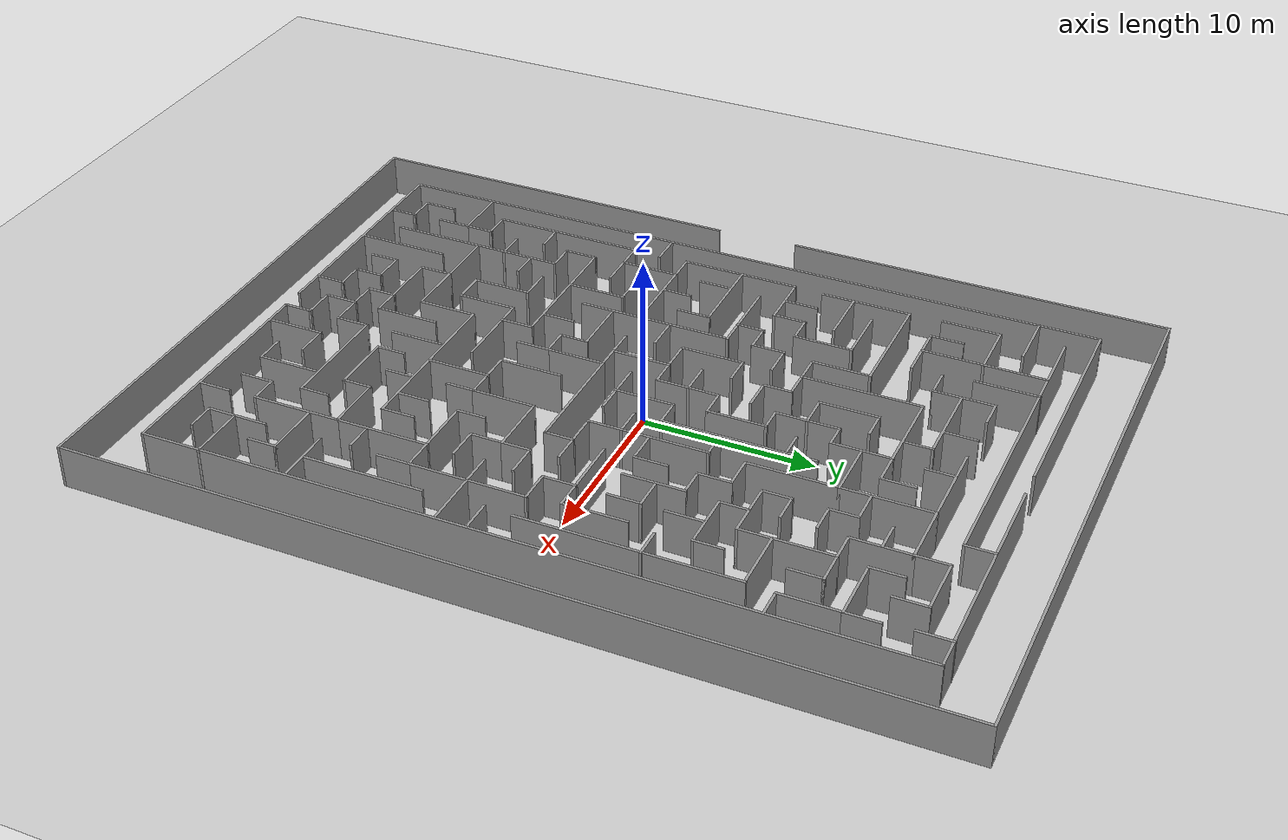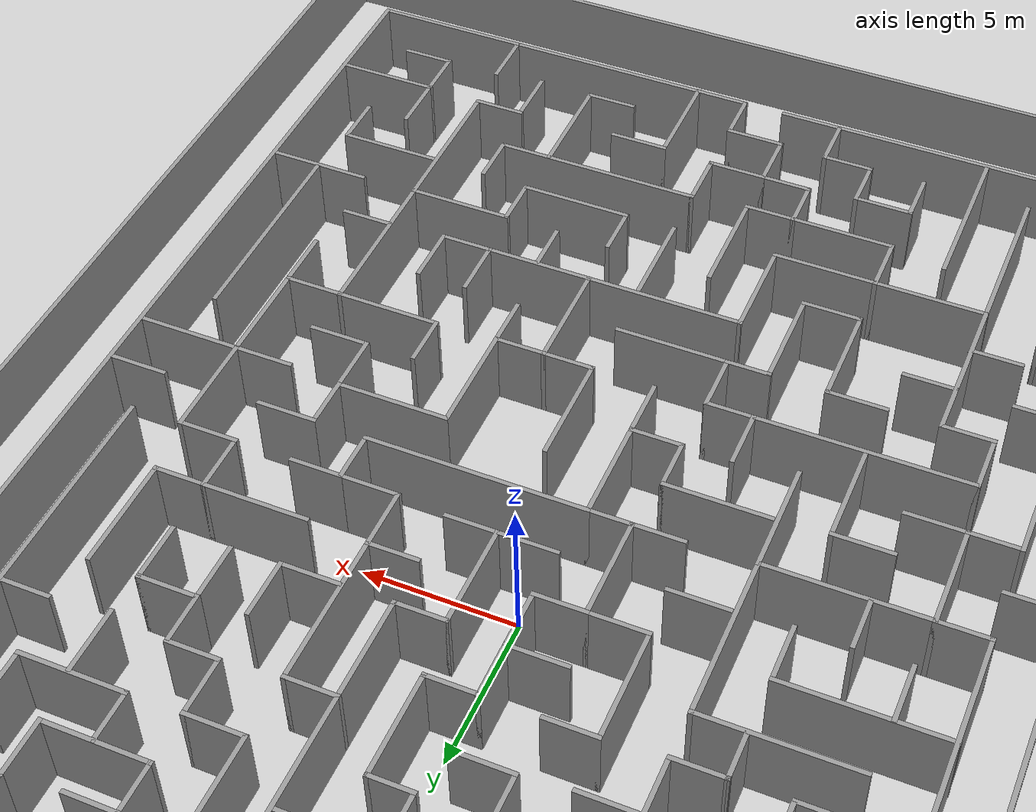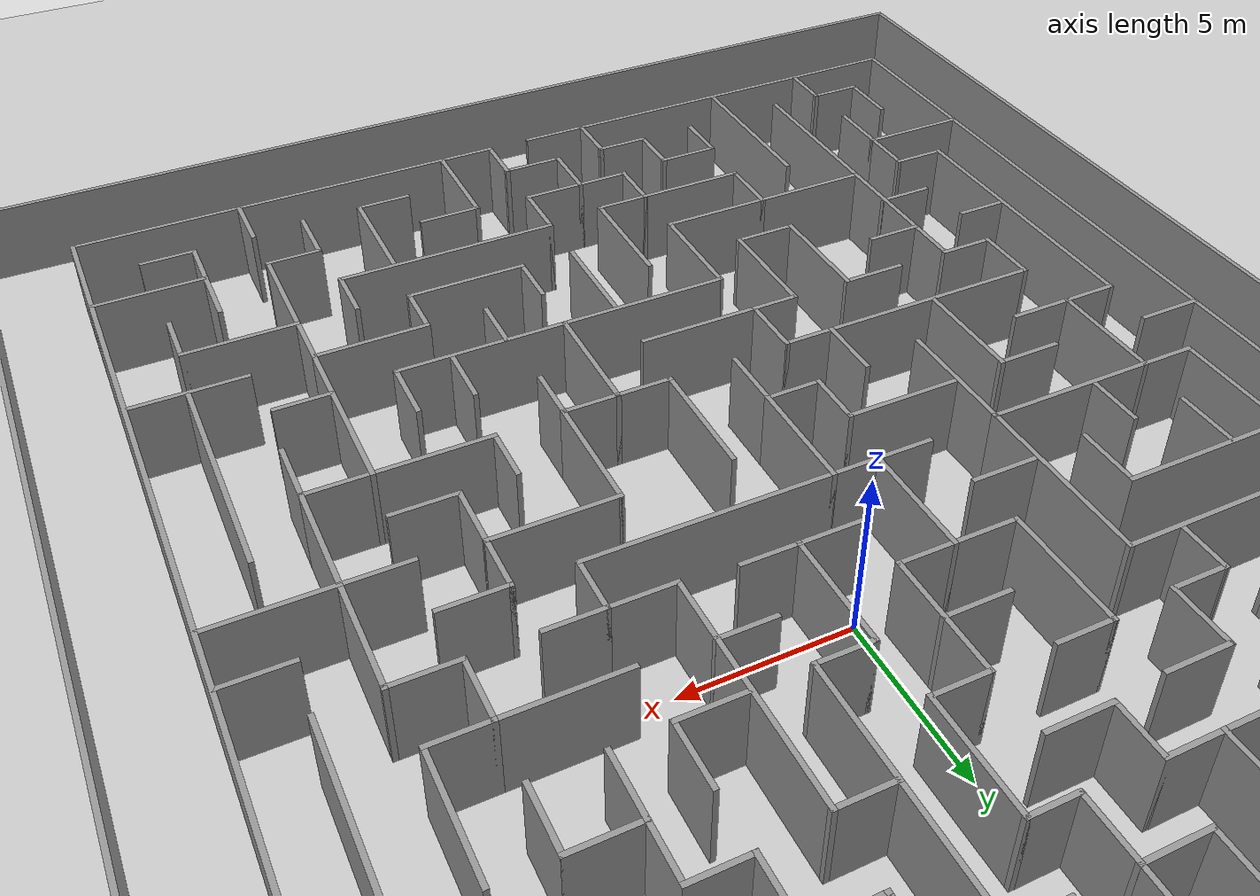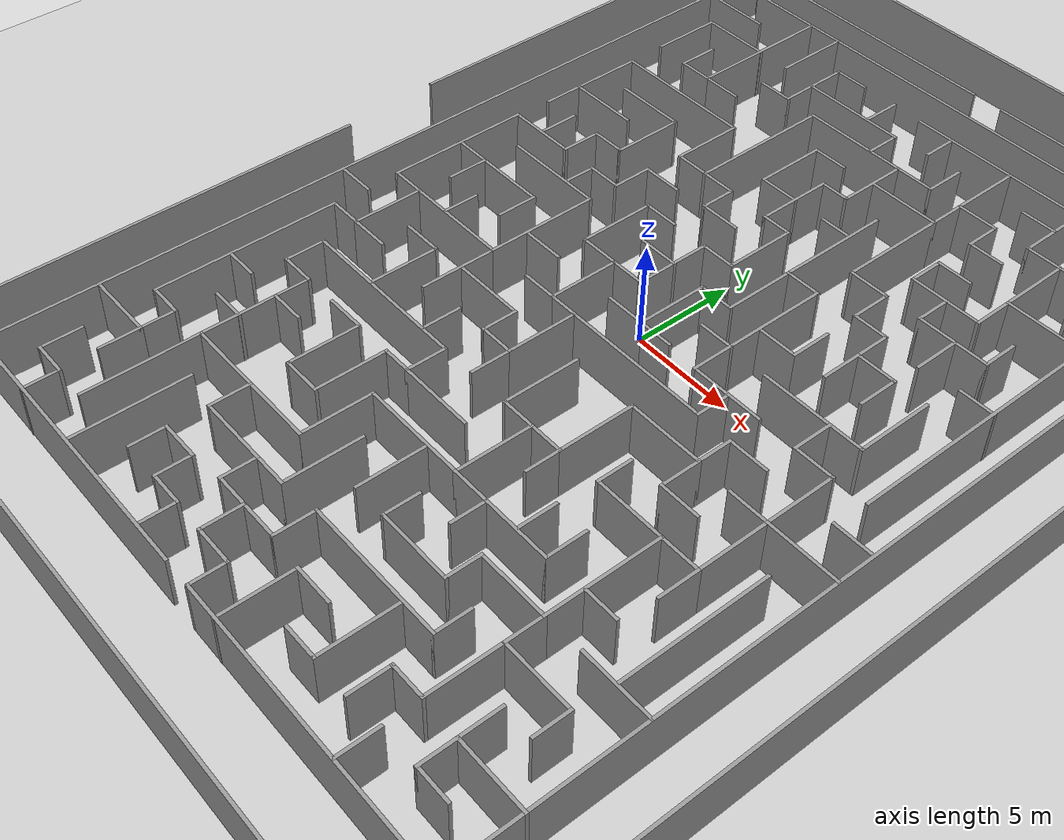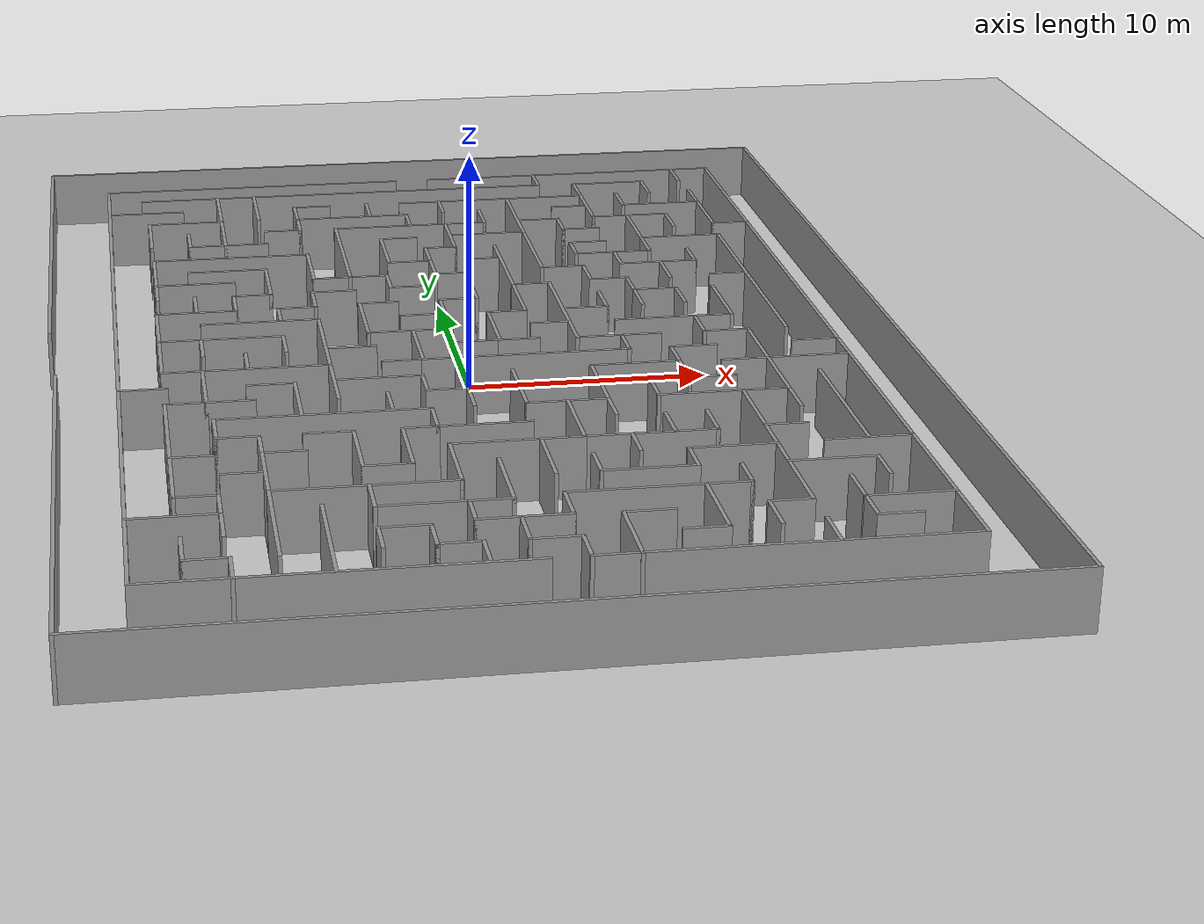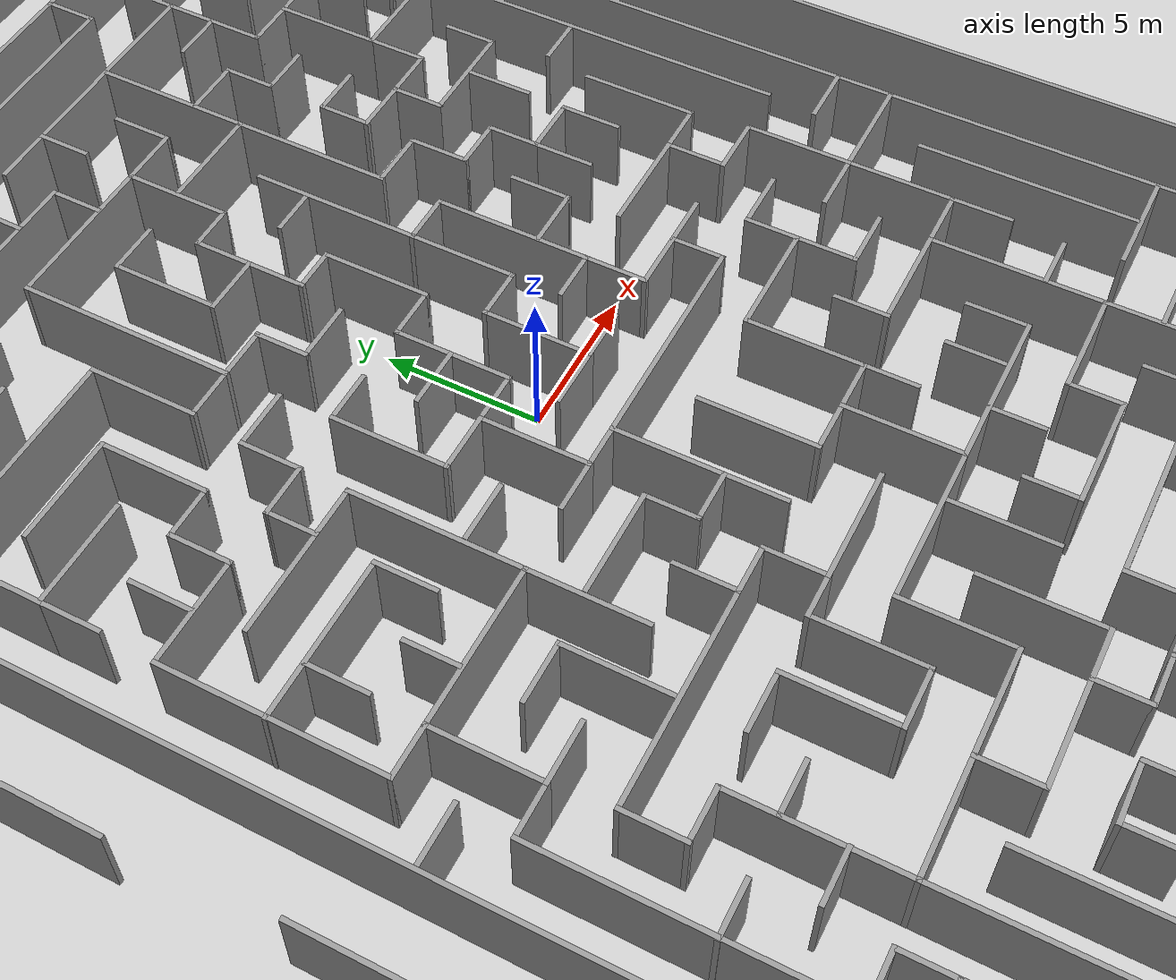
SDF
<sdf version="1.6">
 <world name="default">
  <light name="sun" type="directional">
   <pose>0 0 10 0 -0 0</pose>
   <diffuse>0.8 0.8 0.8 1</diffuse>
   <specular>0.1 0.1 0.1 1</specular>
   <attenuation>
    <range>1000</range>
    <constant>0.9</constant>
    <linear>0.01</linear>
    <quadratic>0.001</quadratic>
   </attenuation>
   <direction>-0.5 0.5 -1</direction>
  </light>
  <model name="ground_plane">
   <static>1</static>
   <link name="link">
    <collision name="collision">
     <geometry><plane><normal>0 0 1</normal><size>100 100</size></plane></geometry>
     <surface><friction><ode><mu>100</mu><mu2>50</mu2></ode></friction></surface>
    </collision>
    <visual name="visual">
     <cast_shadows>0</cast_shadows>
     <geometry><plane><normal>0 0 1</normal><size>100 100</size></plane></geometry>
     <material>
      <script><uri>file://media/materials/scripts/gazebo.material</uri><name>Gazebo/Grey</name></script>
     </material>
    </visual>
   </link>
  </model>
  <gravity>0 0 -9.8</gravity>
  <magnetic_field>6e-06 2.3e-05 -4.2e-05</magnetic_field>
  <atmosphere type="adiabatic"/>
  <physics name="default_physics" default="0" type="ode">
   <max_step_size>0.001</max_step_size>
   <real_time_factor>1</real_time_factor>
   <real_time_update_rate>1000</real_time_update_rate>
  </physics>
  <scene><ambient>0.4 0.4 0.4 1</ambient><background>0.7 0.7 0.7 1</background><shadows>1</shadows></scene>
  <spherical_coordinates>
   <surface_model>EARTH_WGS84</surface_model>
   <latitude_deg>0</latitude_deg>
   <longitude_deg>0</longitude_deg>
   <elevation>0</elevation>
   <heading_deg>0</heading_deg>
  </spherical_coordinates>
  <model name="navigation-maze">
   <pose>0.2351 -0.2528 0 0 -0 0</pose>
   <link name="Wall_101">
    <collision name="Wall_101_Collision">
     <geometry><box><size>1.75 0.15 2.5</size></box></geometry>
     <pose>0 0 1.25 0 -0 0</pose>
    </collision>
    <visual name="Wall_101_Visual">
     <pose>0 0 1.25 0 -0 0</pose>
     <geometry><box><size>1.75 0.15 2.5</size></box></geometry>
     <material>
      <script><uri>file://media/materials/scripts/gazebo.material</uri><name>Gazebo/Grey</name></script>
      <ambient>1 1 1 1</ambient>
     </material>
    </visual>
    <pose>-12.2054 -11.2783 0 0 -0 0</pose>
   </link>
   <link name="Wall_103">
    <collision name="Wall_103_Collision">
     <geometry><box><size>2 0.15 2.5</size></box></geometry>
     <pose>0 0 1.25 0 -0 0</pose>
    </collision>
    <visual name="Wall_103_Visual">
     <pose>0 0 1.25 0 -0 0</pose>
     <geometry><box><size>2 0.15 2.5</size></box></geometry>
     <material>
      <script><uri>file://media/materials/scripts/gazebo.material</uri><name>Gazebo/Grey</name></script>
      <ambient>1 1 1 1</ambient>
     </material>
    </visual>
    <pose>-10.462 -6.02334 0 0 -0 0</pose>
   </link>
   <link name="Wall_105">
    <collision name="Wall_105_Collision">
     <geometry><box><size>5.25 0.15 2.5</size></box></geometry>
     <pose>0 0 1.25 0 -0 0</pose>
    </collision>
    <visual name="Wall_105_Visual">
     <pose>0 0 1.25 0 -0 0</pose>
     <geometry><box><size>5.25 0.15 2.5</size></box></geometry>
     <material>
      <script><uri>file://media/materials/scripts/gazebo.material</uri><name>Gazebo/Grey</name></script>
      <ambient>1 1 1 1</ambient>
     </material>
    </visual>
    <pose>-8.83704 -2.67334 0 0 -0 0</pose>
   </link>
   <link name="Wall_106">
    <collision name="Wall_106_Collision">
     <geometry><box><size>5.5 0.15 2.5</size></box></geometry>
     <pose>0 0 1.25 0 -0 0</pose>
    </collision>
    <visual name="Wall_106_Visual">
     <pose>0 0 1.25 0 -0 0</pose>
     <geometry><box><size>5.5 0.15 2.5</size></box></geometry>
     <material>
      <script><uri>file://media/materials/scripts/gazebo.material</uri><name>Gazebo/Grey</name></script>
      <ambient>1 1 1 1</ambient>
     </material>
    </visual>
    <pose>-6.28704 0.001663 0 0 -0 1.5708</pose>
   </link>
   <link name="Wall_107">
    <collision name="Wall_107_Collision">
     <geometry><box><size>5 0.15 2.5</size></box></geometry>
     <pose>0 0 1.25 0 -0 0</pose>
    </collision>
    <visual name="Wall_107_Visual">
     <pose>0 0 1.25 0 -0 0</pose>
     <geometry><box><size>5 0.15 2.5</size></box></geometry>
     <material>
      <script><uri>file://media/materials/scripts/gazebo.material</uri><name>Gazebo/Grey</name></script>
      <ambient>1 1 1 1</ambient>
     </material>
    </visual>
    <pose>-8.71204 2.67666 0 0 -0 3.14159</pose>
   </link>
   <link name="Wall_109">
    <collision name="Wall_109_Collision">
     <geometry><box><size>2 0.15 2.5</size></box></geometry>
     <pose>0 0 1.25 0 -0 0</pose>
    </collision>
    <visual name="Wall_109_Visual">
     <pose>0 0 1.25 0 -0 0</pose>
     <geometry><box><size>2 0.15 2.5</size></box></geometry>
     <material>
      <script><uri>file://media/materials/scripts/gazebo.material</uri><name>Gazebo/Grey</name></script>
      <ambient>1 1 1 1</ambient>
     </material>
    </visual>
    <pose>-5.2054 -0.836643 0 0 -0 0</pose>
   </link>
   <link name="Wall_111">
    <collision name="Wall_111_Collision">
     <geometry><box><size>1.67297 0.15 2.5</size></box></geometry>
     <pose>0 0 1.25 0 -0 0</pose>
    </collision>
    <visual name="Wall_111_Visual">
     <pose>0 0 1.25 0 -0 0</pose>
     <geometry><box><size>1.67297 0.15 2.5</size></box></geometry>
     <material>
      <script><uri>file://media/materials/scripts/gazebo.material</uri><name>Gazebo/Grey</name></script>
      <ambient>1 1 1 1</ambient>
     </material>
    </visual>
    <pose>-7.86144 3.43937 0 0 -0 1.57161</pose>
   </link>
   <link name="Wall_112">
    <collision name="Wall_112_Collision">
     <geometry><box><size>1.75 0.15 2.5</size></box></geometry>
     <pose>0 0 1.25 0 -0 0</pose>
    </collision>
    <visual name="Wall_112_Visual">
     <pose>0 0 1.25 0 -0 0</pose>
     <geometry><box><size>1.75 0.15 2.5</size></box></geometry>
     <material>
      <script><uri>file://media/materials/scripts/gazebo.material</uri><name>Gazebo/Grey</name></script>
      <ambient>1 1 1 1</ambient>
     </material>
    </visual>
    <pose>-7.06206 4.20085 0 0 -0 0</pose>
   </link>
   <link name="Wall_113">
    <collision name="Wall_113_Collision">
     <geometry><box><size>2 0.15 2.5</size></box></geometry>
     <pose>0 0 1.25 0 -0 0</pose>
    </collision>
    <visual name="Wall_113_Visual">
     <pose>0 0 1.25 0 -0 0</pose>
     <geometry><box><size>2 0.15 2.5</size></box></geometry>
     <material>
      <script><uri>file://media/materials/scripts/gazebo.material</uri><name>Gazebo/Grey</name></script>
      <ambient>1 1 1 1</ambient>
     </material>
    </visual>
    <pose>-6.26206 5.12584 0 0 -0 1.5708</pose>
   </link>
   <link name="Wall_114">
    <collision name="Wall_114_Collision">
     <geometry><box><size>2 0.15 2.5</size></box></geometry>
     <pose>0 0 1.25 0 -0 0</pose>
    </collision>
    <visual name="Wall_114_Visual">
     <pose>0 0 1.25 0 -0 0</pose>
     <geometry><box><size>2 0.15 2.5</size></box></geometry>
     <material>
      <script><uri>file://media/materials/scripts/gazebo.material</uri><name>Gazebo/Grey</name></script>
      <ambient>1 1 1 1</ambient>
     </material>
    </visual>
    <pose>-5.33706 6.05084 0 0 -0 0</pose>
   </link>
   <link name="Wall_116">
    <collision name="Wall_116_Collision">
     <geometry><box><size>5.25 0.15 2.5</size></box></geometry>
     <pose>0 0 1.25 0 -0 0</pose>
    </collision>
    <visual name="Wall_116_Visual">
     <pose>0 0 1.25 0 -0 0</pose>
     <geometry><box><size>5.25 0.15 2.5</size></box></geometry>
     <material>
      <script><uri>file://media/materials/scripts/gazebo.material</uri><name>Gazebo/Grey</name></script>
      <ambient>1 1 1 1</ambient>
     </material>
    </visual>
    <pose>-10.4554 0.869178 0 0 -0 0</pose>
   </link>
   <link name="Wall_117">
    <collision name="Wall_117_Collision">
     <geometry><box><size>2 0.15 2.5</size></box></geometry>
     <pose>0 0 1.25 0 -0 0</pose>
    </collision>
    <visual name="Wall_117_Visual">
     <pose>0 0 1.25 0 -0 0</pose>
     <geometry><box><size>2 0.15 2.5</size></box></geometry>
     <material>
      <script><uri>file://media/materials/scripts/gazebo.material</uri><name>Gazebo/Grey</name></script>
      <ambient>1 1 1 1</ambient>
     </material>
    </visual>
    <pose>-7.90537 -0.055822 0 0 0 -1.5708</pose>
   </link>
   <link name="Wall_119">
    <collision name="Wall_119_Collision">
     <geometry><box><size>2 0.15 2.5</size></box></geometry>
     <pose>0 0 1.25 0 -0 0</pose>
    </collision>
    <visual name="Wall_119_Visual">
     <pose>0 0 1.25 0 -0 0</pose>
     <geometry><box><size>2 0.15 2.5</size></box></geometry>
     <material>
      <script><uri>file://media/materials/scripts/gazebo.material</uri><name>Gazebo/Grey</name></script>
      <ambient>1 1 1 1</ambient>
     </material>
    </visual>
    <pose>-11.2737 -0.081668 0 0 0 -1.5708</pose>
   </link>
   <link name="Wall_121">
    <collision name="Wall_121_Collision">
     <geometry><box><size>1.75 0.15 2.5</size></box></geometry>
     <pose>0 0 1.25 0 -0 0</pose>
    </collision>
    <visual name="Wall_121_Visual">
     <pose>0 0 1.25 0 -0 0</pose>
     <geometry><box><size>1.75 0.15 2.5</size></box></geometry>
     <material>
      <script><uri>file://media/materials/scripts/gazebo.material</uri><name>Gazebo/Grey</name></script>
      <ambient>1 1 1 1</ambient>
     </material>
    </visual>
    <pose>-9.56789 -1.79172 0 0 0 -1.5708</pose>
   </link>
   <link name="Wall_123">
    <collision name="Wall_123_Collision">
     <geometry><box><size>2 0.15 2.5</size></box></geometry>
     <pose>0 0 1.25 0 -0 0</pose>
    </collision>
    <visual name="Wall_123_Visual">
     <pose>0 0 1.25 0 -0 0</pose>
     <geometry><box><size>2 0.15 2.5</size></box></geometry>
     <material>
      <script><uri>file://media/materials/scripts/gazebo.material</uri><name>Gazebo/Grey</name></script>
      <ambient>1 1 1 1</ambient>
     </material>
    </visual>
    <pose>-13.7862 -4.35167 0 0 -0 0</pose>
   </link>
   <link name="Wall_125">
    <collision name="Wall_125_Collision">
     <geometry><box><size>3.75 0.15 2.5</size></box></geometry>
     <pose>0 0 1.25 0 -0 0</pose>
    </collision>
    <visual name="Wall_125_Visual">
     <pose>0 0 1.25 0 -0 0</pose>
     <geometry><box><size>3.75 0.15 2.5</size></box></geometry>
     <material>
      <script><uri>file://media/materials/scripts/gazebo.material</uri><name>Gazebo/Grey</name></script>
      <ambient>1 1 1 1</ambient>
     </material>
    </visual>
    <pose>-6.28704 -4.47334 0 0 0 -1.5708</pose>
   </link>
   <link name="Wall_127">
    <collision name="Wall_127_Collision">
     <geometry><box><size>3.5 0.15 2.5</size></box></geometry>
     <pose>0 0 1.25 0 -0 0</pose>
    </collision>
    <visual name="Wall_127_Visual">
     <pose>0 0 1.25 0 -0 0</pose>
     <geometry><box><size>3.5 0.15 2.5</size></box></geometry>
     <material>
      <script><uri>file://media/materials/scripts/gazebo.material</uri><name>Gazebo/Grey</name></script>
      <ambient>1 1 1 1</ambient>
     </material>
    </visual>
    <pose>-4.4554 -4.35167 0 0 -0 0</pose>
   </link>
   <link name="Wall_128">
    <collision name="Wall_128_Collision">
     <geometry><box><size>1.75 0.15 2.5</size></box></geometry>
     <pose>0 0 1.25 0 -0 0</pose>
    </collision>
    <visual name="Wall_128_Visual">
     <pose>0 0 1.25 0 -0 0</pose>
     <geometry><box><size>1.75 0.15 2.5</size></box></geometry>
     <material>
      <script><uri>file://media/materials/scripts/gazebo.material</uri><name>Gazebo/Grey</name></script>
      <ambient>1 1 1 1</ambient>
     </material>
    </visual>
    <pose>-2.7804 -5.15167 0 0 0 -1.5708</pose>
   </link>
   <link name="Wall_129">
    <collision name="Wall_129_Collision">
     <geometry><box><size>1.75 0.15 2.5</size></box></geometry>
     <pose>0 0 1.25 0 -0 0</pose>
    </collision>
    <visual name="Wall_129_Visual">
     <pose>0 0 1.25 0 -0 0</pose>
     <geometry><box><size>1.75 0.15 2.5</size></box></geometry>
     <material>
      <script><uri>file://media/materials/scripts/gazebo.material</uri><name>Gazebo/Grey</name></script>
      <ambient>1 1 1 1</ambient>
     </material>
    </visual>
    <pose>-1.9804 -5.95167 0 0 -0 0</pose>
   </link>
   <link name="Wall_130">
    <collision name="Wall_130_Collision">
     <geometry><box><size>3.5 0.15 2.5</size></box></geometry>
     <pose>0 0 1.25 0 -0 0</pose>
    </collision>
    <visual name="Wall_130_Visual">
     <pose>0 0 1.25 0 -0 0</pose>
     <geometry><box><size>3.5 0.15 2.5</size></box></geometry>
     <material>
      <script><uri>file://media/materials/scripts/gazebo.material</uri><name>Gazebo/Grey</name></script>
      <ambient>1 1 1 1</ambient>
     </material>
    </visual>
    <pose>-1.1804 -4.27667 0 0 -0 1.5708</pose>
   </link>
   <link name="Wall_131">
    <collision name="Wall_131_Collision">
     <geometry><box><size>1.5 0.15 2.5</size></box></geometry>
     <pose>0 0 1.25 0 -0 0</pose>
    </collision>
    <visual name="Wall_131_Visual">
     <pose>0 0 1.25 0 -0 0</pose>
     <geometry><box><size>1.5 0.15 2.5</size></box></geometry>
     <material>
      <script><uri>file://media/materials/scripts/gazebo.material</uri><name>Gazebo/Grey</name></script>
      <ambient>1 1 1 1</ambient>
     </material>
    </visual>
    <pose>-1.8554 -2.60167 0 0 -0 3.14159</pose>
   </link>
   <link name="Wall_132">
    <collision name="Wall_132_Collision">
     <geometry><box><size>3.5 0.15 2.5</size></box></geometry>
     <pose>0 0 1.25 0 -0 0</pose>
    </collision>
    <visual name="Wall_132_Visual">
     <pose>0 0 1.25 0 -0 0</pose>
     <geometry><box><size>3.5 0.15 2.5</size></box></geometry>
     <material>
      <script><uri>file://media/materials/scripts/gazebo.material</uri><name>Gazebo/Grey</name></script>
      <ambient>1 1 1 1</ambient>
     </material>
    </visual>
    <pose>-2.5304 -0.926668 0 0 -0 1.5708</pose>
   </link>
   <link name="Wall_133">
    <collision name="Wall_133_Collision">
     <geometry><box><size>2 0.15 2.5</size></box></geometry>
     <pose>0 0 1.25 0 -0 0</pose>
    </collision>
    <visual name="Wall_133_Visual">
     <pose>0 0 1.25 0 -0 0</pose>
     <geometry><box><size>2 0.15 2.5</size></box></geometry>
     <material>
      <script><uri>file://media/materials/scripts/gazebo.material</uri><name>Gazebo/Grey</name></script>
      <ambient>1 1 1 1</ambient>
     </material>
    </visual>
    <pose>-3.4554 0.748332 0 0 -0 3.14159</pose>
   </link>
   <link name="Wall_134">
    <collision name="Wall_134_Collision">
     <geometry><box><size>3.75 0.15 2.5</size></box></geometry>
     <pose>0 0 1.25 0 -0 0</pose>
    </collision>
    <visual name="Wall_134_Visual">
     <pose>0 0 1.25 0 -0 0</pose>
     <geometry><box><size>3.75 0.15 2.5</size></box></geometry>
     <material>
      <script><uri>file://media/materials/scripts/gazebo.material</uri><name>Gazebo/Grey</name></script>
      <ambient>1 1 1 1</ambient>
     </material>
    </visual>
    <pose>-4.3804 2.54833 0 0 -0 1.5708</pose>
   </link>
   <link name="Wall_135">
    <collision name="Wall_135_Collision">
     <geometry><box><size>1.75 0.15 2.5</size></box></geometry>
     <pose>0 0 1.25 0 -0 0</pose>
    </collision>
    <visual name="Wall_135_Visual">
     <pose>0 0 1.25 0 -0 0</pose>
     <geometry><box><size>1.75 0.15 2.5</size></box></geometry>
     <material>
      <script><uri>file://media/materials/scripts/gazebo.material</uri><name>Gazebo/Grey</name></script>
      <ambient>1 1 1 1</ambient>
     </material>
    </visual>
    <pose>-3.5804 4.34833 0 0 -0 0</pose>
   </link>
   <link name="Wall_137">
    <collision name="Wall_137_Collision">
     <geometry><box><size>2 0.15 2.5</size></box></geometry>
     <pose>0 0 1.25 0 -0 0</pose>
    </collision>
    <visual name="Wall_137_Visual">
     <pose>0 0 1.25 0 -0 0</pose>
     <geometry><box><size>2 0.15 2.5</size></box></geometry>
     <material>
      <script><uri>file://media/materials/scripts/gazebo.material</uri><name>Gazebo/Grey</name></script>
      <ambient>1 1 1 1</ambient>
     </material>
    </visual>
    <pose>-1.1804 -6.87667 0 0 0 -1.5708</pose>
   </link>
   <link name="Wall_139">
    <collision name="Wall_139_Collision">
     <geometry><box><size>1.75 0.15 2.5</size></box></geometry>
     <pose>0 0 1.25 0 -0 0</pose>
    </collision>
    <visual name="Wall_139_Visual">
     <pose>0 0 1.25 0 -0 0</pose>
     <geometry><box><size>1.75 0.15 2.5</size></box></geometry>
     <material>
      <script><uri>file://media/materials/scripts/gazebo.material</uri><name>Gazebo/Grey</name></script>
      <ambient>1 1 1 1</ambient>
     </material>
    </visual>
    <pose>-1.7304 0.748332 0 0 -0 0</pose>
   </link>
   <link name="Wall_140">
    <collision name="Wall_140_Collision">
     <geometry><box><size>3.75 0.15 2.5</size></box></geometry>
     <pose>0 0 1.25 0 -0 0</pose>
    </collision>
    <visual name="Wall_140_Visual">
     <pose>0 0 1.25 0 -0 0</pose>
     <geometry><box><size>3.75 0.15 2.5</size></box></geometry>
     <material>
      <script><uri>file://media/materials/scripts/gazebo.material</uri><name>Gazebo/Grey</name></script>
      <ambient>1 1 1 1</ambient>
     </material>
    </visual>
    <pose>-0.930398 2.54833 0 0 -0 1.5708</pose>
   </link>
   <link name="Wall_141">
    <collision name="Wall_141_Collision">
     <geometry><box><size>1.75 0.15 2.5</size></box></geometry>
     <pose>0 0 1.25 0 -0 0</pose>
    </collision>
    <visual name="Wall_141_Visual">
     <pose>0 0 1.25 0 -0 0</pose>
     <geometry><box><size>1.75 0.15 2.5</size></box></geometry>
     <material>
      <script><uri>file://media/materials/scripts/gazebo.material</uri><name>Gazebo/Grey</name></script>
      <ambient>1 1 1 1</ambient>
     </material>
    </visual>
    <pose>-0.130398 4.34833 0 0 -0 0</pose>
   </link>
   <link name="Wall_142">
    <collision name="Wall_142_Collision">
     <geometry><box><size>3.5 0.15 2.5</size></box></geometry>
     <pose>0 0 1.25 0 -0 0</pose>
    </collision>
    <visual name="Wall_142_Visual">
     <pose>0 0 1.25 0 -0 0</pose>
     <geometry><box><size>3.5 0.15 2.5</size></box></geometry>
     <material>
      <script><uri>file://media/materials/scripts/gazebo.material</uri><name>Gazebo/Grey</name></script>
      <ambient>1 1 1 1</ambient>
     </material>
    </visual>
    <pose>0.669602 6.02333 0 0 -0 1.5708</pose>
   </link>
   <link name="Wall_143">
    <collision name="Wall_143_Collision">
     <geometry><box><size>1.5 0.15 2.5</size></box></geometry>
     <pose>0 0 1.25 0 -0 0</pose>
    </collision>
    <visual name="Wall_143_Visual">
     <pose>0 0 1.25 0 -0 0</pose>
     <geometry><box><size>1.5 0.15 2.5</size></box></geometry>
     <material>
      <script><uri>file://media/materials/scripts/gazebo.material</uri><name>Gazebo/Grey</name></script>
      <ambient>1 1 1 1</ambient>
     </material>
    </visual>
    <pose>-0.005398 7.69833 0 0 -0 3.14159</pose>
   </link>
   <link name="Wall_144">
    <collision name="Wall_144_Collision">
     <geometry><box><size>3.75 0.15 2.5</size></box></geometry>
     <pose>0 0 1.25 0 -0 0</pose>
    </collision>
    <visual name="Wall_144_Visual">
     <pose>0 0 1.25 0 -0 0</pose>
     <geometry><box><size>3.75 0.15 2.5</size></box></geometry>
     <material>
      <script><uri>file://media/materials/scripts/gazebo.material</uri><name>Gazebo/Grey</name></script>
      <ambient>1 1 1 1</ambient>
     </material>
    </visual>
    <pose>-0.680398 9.49833 0 0 -0 1.5708</pose>
   </link>
   <link name="Wall_145">
    <collision name="Wall_145_Collision">
     <geometry><box><size>1.5 0.15 2.5</size></box></geometry>
     <pose>0 0 1.25 0 -0 0</pose>
    </collision>
    <visual name="Wall_145_Visual">
     <pose>0 0 1.25 0 -0 0</pose>
     <geometry><box><size>1.5 0.15 2.5</size></box></geometry>
     <material>
      <script><uri>file://media/materials/scripts/gazebo.material</uri><name>Gazebo/Grey</name></script>
      <ambient>1 1 1 1</ambient>
     </material>
    </visual>
    <pose>-0.005398 11.2983 0 0 -0 0</pose>
   </link>
   <link name="Wall_146">
    <collision name="Wall_146_Collision">
     <geometry><box><size>3.5 0.15 2.5</size></box></geometry>
     <pose>0 0 1.25 0 -0 0</pose>
    </collision>
    <visual name="Wall_146_Visual">
     <pose>0 0 1.25 0 -0 0</pose>
     <geometry><box><size>3.5 0.15 2.5</size></box></geometry>
     <material>
      <script><uri>file://media/materials/scripts/gazebo.material</uri><name>Gazebo/Grey</name></script>
      <ambient>1 1 1 1</ambient>
     </material>
    </visual>
    <pose>0.669602 12.9733 0 0 -0 1.5708</pose>
   </link>
   <link name="Wall_147">
    <collision name="Wall_147_Collision">
     <geometry><box><size>5.25 0.15 2.5</size></box></geometry>
     <pose>0 0 1.25 0 -0 0</pose>
    </collision>
    <visual name="Wall_147_Visual">
     <pose>0 0 1.25 0 -0 0</pose>
     <geometry><box><size>5.25 0.15 2.5</size></box></geometry>
     <material>
      <script><uri>file://media/materials/scripts/gazebo.material</uri><name>Gazebo/Grey</name></script>
      <ambient>1 1 1 1</ambient>
     </material>
    </visual>
    <pose>-1.8804 14.6483 0 0 -0 3.14159</pose>
   </link>
   <link name="Wall_148">
    <collision name="Wall_148_Collision">
     <geometry><box><size>7 0.15 2.5</size></box></geometry>
     <pose>0 0 1.25 0 -0 0</pose>
    </collision>
    <visual name="Wall_148_Visual">
     <pose>0 0 1.25 0 -0 0</pose>
     <geometry><box><size>7 0.15 2.5</size></box></geometry>
     <material>
      <script><uri>file://media/materials/scripts/gazebo.material</uri><name>Gazebo/Grey</name></script>
      <ambient>1 1 1 1</ambient>
     </material>
    </visual>
    <pose>-4.4304 11.2233 0 0 0 -1.5708</pose>
   </link>
   <link name="Wall_149">
    <collision name="Wall_149_Collision">
     <geometry><box><size>1.75 0.15 2.5</size></box></geometry>
     <pose>0 0 1.25 0 -0 0</pose>
    </collision>
    <visual name="Wall_149_Visual">
     <pose>0 0 1.25 0 -0 0</pose>
     <geometry><box><size>1.75 0.15 2.5</size></box></geometry>
     <material>
      <script><uri>file://media/materials/scripts/gazebo.material</uri><name>Gazebo/Grey</name></script>
      <ambient>1 1 1 1</ambient>
     </material>
    </visual>
    <pose>-5.2304 7.79833 0 0 -0 3.14159</pose>
   </link>
   <link name="Wall_150">
    <collision name="Wall_150_Collision">
     <geometry><box><size>3.5 0.15 2.5</size></box></geometry>
     <pose>0 0 1.25 0 -0 0</pose>
    </collision>
    <visual name="Wall_150_Visual">
     <pose>0 0 1.25 0 -0 0</pose>
     <geometry><box><size>3.5 0.15 2.5</size></box></geometry>
     <material>
      <script><uri>file://media/materials/scripts/gazebo.material</uri><name>Gazebo/Grey</name></script>
      <ambient>1 1 1 1</ambient>
     </material>
    </visual>
    <pose>-6.0304 9.47333 0 0 -0 1.5708</pose>
   </link>
   <link name="Wall_151">
    <collision name="Wall_151_Collision">
     <geometry><box><size>7 0.15 2.5</size></box></geometry>
     <pose>0 0 1.25 0 -0 0</pose>
    </collision>
    <visual name="Wall_151_Visual">
     <pose>0 0 1.25 0 -0 0</pose>
     <geometry><box><size>7 0.15 2.5</size></box></geometry>
     <material>
      <script><uri>file://media/materials/scripts/gazebo.material</uri><name>Gazebo/Grey</name></script>
      <ambient>1 1 1 1</ambient>
     </material>
    </visual>
    <pose>-9.4554 11.1483 0 0 -0 3.14159</pose>
   </link>
   <link name="Wall_152">
    <collision name="Wall_152_Collision">
     <geometry><box><size>3.5 0.15 2.5</size></box></geometry>
     <pose>0 0 1.25 0 -0 0</pose>
    </collision>
    <visual name="Wall_152_Visual">
     <pose>0 0 1.25 0 -0 0</pose>
     <geometry><box><size>3.5 0.15 2.5</size></box></geometry>
     <material>
      <script><uri>file://media/materials/scripts/gazebo.material</uri><name>Gazebo/Grey</name></script>
      <ambient>1 1 1 1</ambient>
     </material>
    </visual>
    <pose>-12.8804 9.47333 0 0 0 -1.5708</pose>
   </link>
   <link name="Wall_153">
    <collision name="Wall_153_Collision">
     <geometry><box><size>3.5 0.15 2.5</size></box></geometry>
     <pose>0 0 1.25 0 -0 0</pose>
    </collision>
    <visual name="Wall_153_Visual">
     <pose>0 0 1.25 0 -0 0</pose>
     <geometry><box><size>3.5 0.15 2.5</size></box></geometry>
     <material>
      <script><uri>file://media/materials/scripts/gazebo.material</uri><name>Gazebo/Grey</name></script>
      <ambient>1 1 1 1</ambient>
     </material>
    </visual>
    <pose>-11.2054 7.79833 0 0 -0 0</pose>
   </link>
   <link name="Wall_155">
    <collision name="Wall_155_Collision">
     <geometry><box><size>2 0.15 2.5</size></box></geometry>
     <pose>0 0 1.25 0 -0 0</pose>
    </collision>
    <visual name="Wall_155_Visual">
     <pose>0 0 1.25 0 -0 0</pose>
     <geometry><box><size>2 0.15 2.5</size></box></geometry>
     <material>
      <script><uri>file://media/materials/scripts/gazebo.material</uri><name>Gazebo/Grey</name></script>
      <ambient>1 1 1 1</ambient>
     </material>
    </visual>
    <pose>-1.60194 9.50167 0 0 -0 3.14159</pose>
   </link>
   <link name="Wall_156">
    <collision name="Wall_156_Collision">
     <geometry><box><size>3.5 0.15 2.5</size></box></geometry>
     <pose>0 0 1.25 0 -0 0</pose>
    </collision>
    <visual name="Wall_156_Visual">
     <pose>0 0 1.25 0 -0 0</pose>
     <geometry><box><size>3.5 0.15 2.5</size></box></geometry>
     <material>
      <script><uri>file://media/materials/scripts/gazebo.material</uri><name>Gazebo/Grey</name></script>
      <ambient>1 1 1 1</ambient>
     </material>
    </visual>
    <pose>-2.52694 11.1767 0 0 -0 1.5708</pose>
   </link>
   <link name="Wall_157">
    <collision name="Wall_157_Collision">
     <geometry><box><size>1.75 0.15 2.5</size></box></geometry>
     <pose>0 0 1.25 0 -0 0</pose>
    </collision>
    <visual name="Wall_157_Visual">
     <pose>0 0 1.25 0 -0 0</pose>
     <geometry><box><size>1.75 0.15 2.5</size></box></geometry>
     <material>
      <script><uri>file://media/materials/scripts/gazebo.material</uri><name>Gazebo/Grey</name></script>
      <ambient>1 1 1 1</ambient>
     </material>
    </visual>
    <pose>-1.72694 12.8517 0 0 -0 0</pose>
   </link>
   <link name="Wall_159">
    <collision name="Wall_159_Collision">
     <geometry><box><size>1.75 0.15 2.5</size></box></geometry>
     <pose>0 0 1.25 0 -0 0</pose>
    </collision>
    <visual name="Wall_159_Visual">
     <pose>0 0 1.25 0 -0 0</pose>
     <geometry><box><size>1.75 0.15 2.5</size></box></geometry>
     <material>
      <script><uri>file://media/materials/scripts/gazebo.material</uri><name>Gazebo/Grey</name></script>
      <ambient>1 1 1 1</ambient>
     </material>
    </visual>
    <pose>-3.6304 7.79833 0 0 -0 0</pose>
   </link>
   <link name="Wall_160">
    <collision name="Wall_160_Collision">
     <geometry><box><size>1.75 0.15 2.5</size></box></geometry>
     <pose>0 0 1.25 0 -0 0</pose>
    </collision>
    <visual name="Wall_160_Visual">
     <pose>0 0 1.25 0 -0 0</pose>
     <geometry><box><size>1.75 0.15 2.5</size></box></geometry>
     <material>
      <script><uri>file://media/materials/scripts/gazebo.material</uri><name>Gazebo/Grey</name></script>
      <ambient>1 1 1 1</ambient>
     </material>
    </visual>
    <pose>-2.8304 6.99833 0 0 0 -1.5708</pose>
   </link>
   <link name="Wall_161">
    <collision name="Wall_161_Collision">
     <geometry><box><size>2 0.15 2.5</size></box></geometry>
     <pose>0 0 1.25 0 -0 0</pose>
    </collision>
    <visual name="Wall_161_Visual">
     <pose>0 0 1.25 0 -0 0</pose>
     <geometry><box><size>2 0.15 2.5</size></box></geometry>
     <material>
      <script><uri>file://media/materials/scripts/gazebo.material</uri><name>Gazebo/Grey</name></script>
      <ambient>1 1 1 1</ambient>
     </material>
    </visual>
    <pose>-1.9054 6.19833 0 0 -0 0</pose>
   </link>
   <link name="Wall_163">
    <collision name="Wall_163_Collision">
     <geometry><box><size>2 0.15 2.5</size></box></geometry>
     <pose>0 0 1.25 0 -0 0</pose>
    </collision>
    <visual name="Wall_163_Visual">
     <pose>0 0 1.25 0 -0 0</pose>
     <geometry><box><size>2 0.15 2.5</size></box></geometry>
     <material>
      <script><uri>file://media/materials/scripts/gazebo.material</uri><name>Gazebo/Grey</name></script>
      <ambient>1 1 1 1</ambient>
     </material>
    </visual>
    <pose>-11.2996 5.17997 0 0 -0 1.5708</pose>
   </link>
   <link name="Wall_165">
    <collision name="Wall_165_Collision">
     <geometry><box><size>2 0.15 2.5</size></box></geometry>
     <pose>0 0 1.25 0 -0 0</pose>
    </collision>
    <visual name="Wall_165_Visual">
     <pose>0 0 1.25 0 -0 0</pose>
     <geometry><box><size>2 0.15 2.5</size></box></geometry>
     <material>
      <script><uri>file://media/materials/scripts/gazebo.material</uri><name>Gazebo/Grey</name></script>
      <ambient>1 1 1 1</ambient>
     </material>
    </visual>
    <pose>-12.8804 6.87333 0 0 0 -1.5708</pose>
   </link>
   <link name="Wall_167">
    <collision name="Wall_167_Collision">
     <geometry><box><size>2 0.15 2.5</size></box></geometry>
     <pose>0 0 1.25 0 -0 0</pose>
    </collision>
    <visual name="Wall_167_Visual">
     <pose>0 0 1.25 0 -0 0</pose>
     <geometry><box><size>2 0.15 2.5</size></box></geometry>
     <material>
      <script><uri>file://media/materials/scripts/gazebo.material</uri><name>Gazebo/Grey</name></script>
      <ambient>1 1 1 1</ambient>
     </material>
    </visual>
    <pose>1.5946 14.6483 0 0 -0 0</pose>
   </link>
   <link name="Wall_168">
    <collision name="Wall_168_Collision">
     <geometry><box><size>2 0.15 2.5</size></box></geometry>
     <pose>0 0 1.25 0 -0 0</pose>
    </collision>
    <visual name="Wall_168_Visual">
     <pose>0 0 1.25 0 -0 0</pose>
     <geometry><box><size>2 0.15 2.5</size></box></geometry>
     <material>
      <script><uri>file://media/materials/scripts/gazebo.material</uri><name>Gazebo/Grey</name></script>
      <ambient>1 1 1 1</ambient>
     </material>
    </visual>
    <pose>2.5196 15.5733 0 0 -0 1.5708</pose>
   </link>
   <link name="Wall_170">
    <collision name="Wall_170_Collision">
     <geometry><box><size>1.75 0.15 2.5</size></box></geometry>
     <pose>0 0 1.25 0 -0 0</pose>
    </collision>
    <visual name="Wall_170_Visual">
     <pose>0 0 1.25 0 -0 0</pose>
     <geometry><box><size>1.75 0.15 2.5</size></box></geometry>
     <material>
      <script><uri>file://media/materials/scripts/gazebo.material</uri><name>Gazebo/Grey</name></script>
      <ambient>1 1 1 1</ambient>
     </material>
    </visual>
    <pose>-0.961243 15.4967 0 0 -0 1.5708</pose>
   </link>
   <link name="Wall_171">
    <collision name="Wall_171_Collision">
     <geometry><box><size>5.25 0.15 2.5</size></box></geometry>
     <pose>0 0 1.25 0 -0 0</pose>
    </collision>
    <visual name="Wall_171_Visual">
     <pose>0 0 1.25 0 -0 0</pose>
     <geometry><box><size>5.25 0.15 2.5</size></box></geometry>
     <material>
      <script><uri>file://media/materials/scripts/gazebo.material</uri><name>Gazebo/Grey</name></script>
      <ambient>1 1 1 1</ambient>
     </material>
    </visual>
    <pose>-3.51124 16.2967 0 0 -0 3.14159</pose>
   </link>
   <link name="Wall_172">
    <collision name="Wall_172_Collision">
     <geometry><box><size>1.75 0.15 2.5</size></box></geometry>
     <pose>0 0 1.25 0 -0 0</pose>
    </collision>
    <visual name="Wall_172_Visual">
     <pose>0 0 1.25 0 -0 0</pose>
     <geometry><box><size>1.75 0.15 2.5</size></box></geometry>
     <material>
      <script><uri>file://media/materials/scripts/gazebo.material</uri><name>Gazebo/Grey</name></script>
      <ambient>1 1 1 1</ambient>
     </material>
    </visual>
    <pose>-6.06124 15.4967 0 0 0 -1.5708</pose>
   </link>
   <link name="Wall_173">
    <collision name="Wall_173_Collision">
     <geometry><box><size>1.75 0.15 2.5</size></box></geometry>
     <pose>0 0 1.25 0 -0 0</pose>
    </collision>
    <visual name="Wall_173_Visual">
     <pose>0 0 1.25 0 -0 0</pose>
     <geometry><box><size>1.75 0.15 2.5</size></box></geometry>
     <material>
      <script><uri>file://media/materials/scripts/gazebo.material</uri><name>Gazebo/Grey</name></script>
      <ambient>1 1 1 1</ambient>
     </material>
    </visual>
    <pose>-6.86124 14.6967 0 0 -0 3.14159</pose>
   </link>
   <link name="Wall_175">
    <collision name="Wall_175_Collision">
     <geometry><box><size>2 0.15 2.5</size></box></geometry>
     <pose>0 0 1.25 0 -0 0</pose>
    </collision>
    <visual name="Wall_175_Visual">
     <pose>0 0 1.25 0 -0 0</pose>
     <geometry><box><size>2 0.15 2.5</size></box></geometry>
     <material>
      <script><uri>file://media/materials/scripts/gazebo.material</uri><name>Gazebo/Grey</name></script>
      <ambient>1 1 1 1</ambient>
     </material>
    </visual>
    <pose>-6.06124 17.2217 0 0 -0 1.5708</pose>
   </link>
   <link name="Wall_176">
    <collision name="Wall_176_Collision">
     <geometry><box><size>1.75 0.15 2.5</size></box></geometry>
     <pose>0 0 1.25 0 -0 0</pose>
    </collision>
    <visual name="Wall_176_Visual">
     <pose>0 0 1.25 0 -0 0</pose>
     <geometry><box><size>1.75 0.15 2.5</size></box></geometry>
     <material>
      <script><uri>file://media/materials/scripts/gazebo.material</uri><name>Gazebo/Grey</name></script>
      <ambient>1 1 1 1</ambient>
     </material>
    </visual>
    <pose>-5.26124 18.1467 0 0 -0 0</pose>
   </link>
   <link name="Wall_178">
    <collision name="Wall_178_Collision">
     <geometry><box><size>2 0.15 2.5</size></box></geometry>
     <pose>0 0 1.25 0 -0 0</pose>
    </collision>
    <visual name="Wall_178_Visual">
     <pose>0 0 1.25 0 -0 0</pose>
     <geometry><box><size>2 0.15 2.5</size></box></geometry>
     <material>
      <script><uri>file://media/materials/scripts/gazebo.material</uri><name>Gazebo/Grey</name></script>
      <ambient>1 1 1 1</ambient>
     </material>
    </visual>
    <pose>-2.64122 17.25 0 0 -0 1.5708</pose>
   </link>
   <link name="Wall_180">
    <collision name="Wall_180_Collision">
     <geometry><box><size>2 0.15 2.5</size></box></geometry>
     <pose>0 0 1.25 0 -0 0</pose>
    </collision>
    <visual name="Wall_180_Visual">
     <pose>0 0 1.25 0 -0 0</pose>
     <geometry><box><size>2 0.15 2.5</size></box></geometry>
     <material>
      <script><uri>file://media/materials/scripts/gazebo.material</uri><name>Gazebo/Grey</name></script>
      <ambient>1 1 1 1</ambient>
     </material>
    </visual>
    <pose>-1.85517 2.60161 0 0 -0 3.14159</pose>
   </link>
   <link name="Wall_182">
    <collision name="Wall_182_Collision">
     <geometry><box><size>1.75 0.15 2.5</size></box></geometry>
     <pose>0 0 1.25 0 -0 0</pose>
    </collision>
    <visual name="Wall_182_Visual">
     <pose>0 0 1.25 0 -0 0</pose>
     <geometry><box><size>1.75 0.15 2.5</size></box></geometry>
     <material>
      <script><uri>file://media/materials/scripts/gazebo.material</uri><name>Gazebo/Grey</name></script>
      <ambient>1 1 1 1</ambient>
     </material>
    </visual>
    <pose>-3.3304 -2.60167 0 0 -0 3.14159</pose>
   </link>
   <link name="Wall_184">
    <collision name="Wall_184_Collision">
     <geometry><box><size>7.25 0.15 2.5</size></box></geometry>
     <pose>0 0 1.25 0 -0 0</pose>
    </collision>
    <visual name="Wall_184_Visual">
     <pose>0 0 1.25 0 -0 0</pose>
     <geometry><box><size>7.25 0.15 2.5</size></box></geometry>
     <material>
      <script><uri>file://media/materials/scripts/gazebo.material</uri><name>Gazebo/Grey</name></script>
      <ambient>1 1 1 1</ambient>
     </material>
    </visual>
    <pose>2.3696 -2.60167 0 0 -0 0</pose>
   </link>
   <link name="Wall_185">
    <collision name="Wall_185_Collision">
     <geometry><box><size>1.75 0.15 2.5</size></box></geometry>
     <pose>0 0 1.25 0 -0 0</pose>
    </collision>
    <visual name="Wall_185_Visual">
     <pose>0 0 1.25 0 -0 0</pose>
     <geometry><box><size>1.75 0.15 2.5</size></box></geometry>
     <material>
      <script><uri>file://media/materials/scripts/gazebo.material</uri><name>Gazebo/Grey</name></script>
      <ambient>1 1 1 1</ambient>
     </material>
    </visual>
    <pose>5.9196 -1.80167 0 0 -0 1.5708</pose>
   </link>
   <link name="Wall_186">
    <collision name="Wall_186_Collision">
     <geometry><box><size>2 0.15 2.5</size></box></geometry>
     <pose>0 0 1.25 0 -0 0</pose>
    </collision>
    <visual name="Wall_186_Visual">
     <pose>0 0 1.25 0 -0 0</pose>
     <geometry><box><size>2 0.15 2.5</size></box></geometry>
     <material>
      <script><uri>file://media/materials/scripts/gazebo.material</uri><name>Gazebo/Grey</name></script>
      <ambient>1 1 1 1</ambient>
     </material>
    </visual>
    <pose>4.9946 -1.00167 0 0 -0 3.14159</pose>
   </link>
   <link name="Wall_187">
    <collision name="Wall_187_Collision">
     <geometry><box><size>7 0.15 2.5</size></box></geometry>
     <pose>0 0 1.25 0 -0 0</pose>
    </collision>
    <visual name="Wall_187_Visual">
     <pose>0 0 1.25 0 -0 0</pose>
     <geometry><box><size>7 0.15 2.5</size></box></geometry>
     <material>
      <script><uri>file://media/materials/scripts/gazebo.material</uri><name>Gazebo/Grey</name></script>
      <ambient>1 1 1 1</ambient>
     </material>
    </visual>
    <pose>4.0696 2.42333 0 0 -0 1.5708</pose>
   </link>
   <link name="Wall_188">
    <collision name="Wall_188_Collision">
     <geometry><box><size>1.75 0.15 2.5</size></box></geometry>
     <pose>0 0 1.25 0 -0 0</pose>
    </collision>
    <visual name="Wall_188_Visual">
     <pose>0 0 1.25 0 -0 0</pose>
     <geometry><box><size>1.75 0.15 2.5</size></box></geometry>
     <material>
      <script><uri>file://media/materials/scripts/gazebo.material</uri><name>Gazebo/Grey</name></script>
      <ambient>1 1 1 1</ambient>
     </material>
    </visual>
    <pose>3.2696 5.84833 0 0 -0 3.14159</pose>
   </link>
   <link name="Wall_189">
    <collision name="Wall_189_Collision">
     <geometry><box><size>3.5 0.15 2.5</size></box></geometry>
     <pose>0 0 1.25 0 -0 0</pose>
    </collision>
    <visual name="Wall_189_Visual">
     <pose>0 0 1.25 0 -0 0</pose>
     <geometry><box><size>3.5 0.15 2.5</size></box></geometry>
     <material>
      <script><uri>file://media/materials/scripts/gazebo.material</uri><name>Gazebo/Grey</name></script>
      <ambient>1 1 1 1</ambient>
     </material>
    </visual>
    <pose>2.4696 4.17333 0 0 0 -1.5708</pose>
   </link>
   <link name="Wall_190">
    <collision name="Wall_190_Collision">
     <geometry><box><size>1.75 0.15 2.5</size></box></geometry>
     <pose>0 0 1.25 0 -0 0</pose>
    </collision>
    <visual name="Wall_190_Visual">
     <pose>0 0 1.25 0 -0 0</pose>
     <geometry><box><size>1.75 0.15 2.5</size></box></geometry>
     <material>
      <script><uri>file://media/materials/scripts/gazebo.material</uri><name>Gazebo/Grey</name></script>
      <ambient>1 1 1 1</ambient>
     </material>
    </visual>
    <pose>1.6696 2.49833 0 0 -0 3.14159</pose>
   </link>
   <link name="Wall_191">
    <collision name="Wall_191_Collision">
     <geometry><box><size>3.5 0.15 2.5</size></box></geometry>
     <pose>0 0 1.25 0 -0 0</pose>
    </collision>
    <visual name="Wall_191_Visual">
     <pose>0 0 1.25 0 -0 0</pose>
     <geometry><box><size>3.5 0.15 2.5</size></box></geometry>
     <material>
      <script><uri>file://media/materials/scripts/gazebo.material</uri><name>Gazebo/Grey</name></script>
      <ambient>1 1 1 1</ambient>
     </material>
    </visual>
    <pose>0.869602 0.823332 0 0 0 -1.5708</pose>
   </link>
   <link name="Wall_192">
    <collision name="Wall_192_Collision">
     <geometry><box><size>2 0.15 2.5</size></box></geometry>
     <pose>0 0 1.25 0 -0 0</pose>
    </collision>
    <visual name="Wall_192_Visual">
     <pose>0 0 1.25 0 -0 0</pose>
     <geometry><box><size>2 0.15 2.5</size></box></geometry>
     <material>
      <script><uri>file://media/materials/scripts/gazebo.material</uri><name>Gazebo/Grey</name></script>
      <ambient>1 1 1 1</ambient>
     </material>
    </visual>
    <pose>-0.055398 -0.851668 0 0 -0 3.14159</pose>
   </link>
   <link name="Wall_194">
    <collision name="Wall_194_Collision">
     <geometry><box><size>1.75 0.15 2.5</size></box></geometry>
     <pose>0 0 1.25 0 -0 0</pose>
    </collision>
    <visual name="Wall_194_Visual">
     <pose>0 0 1.25 0 -0 0</pose>
     <geometry><box><size>1.75 0.15 2.5</size></box></geometry>
     <material>
      <script><uri>file://media/materials/scripts/gazebo.material</uri><name>Gazebo/Grey</name></script>
      <ambient>1 1 1 1</ambient>
     </material>
    </visual>
    <pose>1.6696 -0.851668 0 0 -0 0</pose>
   </link>
   <link name="Wall_196">
    <collision name="Wall_196_Collision">
     <geometry><box><size>1.71692 0.15 2.5</size></box></geometry>
     <pose>0 0 1.25 0 -0 0</pose>
    </collision>
    <visual name="Wall_196_Visual">
     <pose>0 0 1.25 0 -0 0</pose>
     <geometry><box><size>1.71692 0.15 2.5</size></box></geometry>
     <material>
      <script><uri>file://media/materials/scripts/gazebo.material</uri><name>Gazebo/Grey</name></script>
      <ambient>1 1 1 1</ambient>
     </material>
    </visual>
    <pose>3.28799 0.921172 0 0 0 -3.14121</pose>
   </link>
   <link name="Wall_198">
    <collision name="Wall_198_Collision">
     <geometry><box><size>1.75 0.15 2.5</size></box></geometry>
     <pose>0 0 1.25 0 -0 0</pose>
    </collision>
    <visual name="Wall_198_Visual">
     <pose>0 0 1.25 0 -0 0</pose>
     <geometry><box><size>1.75 0.15 2.5</size></box></geometry>
     <material>
      <script><uri>file://media/materials/scripts/gazebo.material</uri><name>Gazebo/Grey</name></script>
      <ambient>1 1 1 1</ambient>
     </material>
    </visual>
    <pose>6.7196 -1.00167 0 0 -0 0</pose>
   </link>
   <link name="Wall_200">
    <collision name="Wall_200_Collision">
     <geometry><box><size>5.5 0.15 2.5</size></box></geometry>
     <pose>0 0 1.25 0 -0 0</pose>
    </collision>
    <visual name="Wall_200_Visual">
     <pose>0 0 1.25 0 -0 0</pose>
     <geometry><box><size>5.5 0.15 2.5</size></box></geometry>
     <material>
      <script><uri>file://media/materials/scripts/gazebo.material</uri><name>Gazebo/Grey</name></script>
      <ambient>1 1 1 1</ambient>
     </material>
    </visual>
    <pose>2.4696 8.52333 0 0 -0 1.5708</pose>
   </link>
   <link name="Wall_202">
    <collision name="Wall_202_Collision">
     <geometry><box><size>1.5 0.15 2.5</size></box></geometry>
     <pose>0 0 1.25 0 -0 0</pose>
    </collision>
    <visual name="Wall_202_Visual">
     <pose>0 0 1.25 0 -0 0</pose>
     <geometry><box><size>1.5 0.15 2.5</size></box></geometry>
     <material>
      <script><uri>file://media/materials/scripts/gazebo.material</uri><name>Gazebo/Grey</name></script>
      <ambient>1 1 1 1</ambient>
     </material>
    </visual>
    <pose>1.66167 9.49853 0 0 -0 3.14159</pose>
   </link>
   <link name="Wall_204">
    <collision name="Wall_204_Collision">
     <geometry><box><size>2 0.15 2.5</size></box></geometry>
     <pose>0 0 1.25 0 -0 0</pose>
    </collision>
    <visual name="Wall_204_Visual">
     <pose>0 0 1.25 0 -0 0</pose>
     <geometry><box><size>2 0.15 2.5</size></box></geometry>
     <material>
      <script><uri>file://media/materials/scripts/gazebo.material</uri><name>Gazebo/Grey</name></script>
      <ambient>1 1 1 1</ambient>
     </material>
    </visual>
    <pose>5.05537 2.52331 0 0 -0 0</pose>
   </link>
   <link name="Wall_205">
    <collision name="Wall_205_Collision">
     <geometry><box><size>2 0.15 2.5</size></box></geometry>
     <pose>0 0 1.25 0 -0 0</pose>
    </collision>
    <visual name="Wall_205_Visual">
     <pose>0 0 1.25 0 -0 0</pose>
     <geometry><box><size>2 0.15 2.5</size></box></geometry>
     <material>
      <script><uri>file://media/materials/scripts/gazebo.material</uri><name>Gazebo/Grey</name></script>
      <ambient>1 1 1 1</ambient>
     </material>
    </visual>
    <pose>5.98038 3.44831 0 0 -0 1.5708</pose>
   </link>
   <link name="Wall_207">
    <collision name="Wall_207_Collision">
     <geometry><box><size>3.5 0.15 2.5</size></box></geometry>
     <pose>0 0 1.25 0 -0 0</pose>
    </collision>
    <visual name="Wall_207_Visual">
     <pose>0 0 1.25 0 -0 0</pose>
     <geometry><box><size>3.5 0.15 2.5</size></box></geometry>
     <material>
      <script><uri>file://media/materials/scripts/gazebo.material</uri><name>Gazebo/Grey</name></script>
      <ambient>1 1 1 1</ambient>
     </material>
    </visual>
    <pose>2.41958 12.9908 0 0 -0 0</pose>
   </link>
   <link name="Wall_208">
    <collision name="Wall_208_Collision">
     <geometry><box><size>5.25 0.15 2.5</size></box></geometry>
     <pose>0 0 1.25 0 -0 0</pose>
    </collision>
    <visual name="Wall_208_Visual">
     <pose>0 0 1.25 0 -0 0</pose>
     <geometry><box><size>5.25 0.15 2.5</size></box></geometry>
     <material>
      <script><uri>file://media/materials/scripts/gazebo.material</uri><name>Gazebo/Grey</name></script>
      <ambient>1 1 1 1</ambient>
     </material>
    </visual>
    <pose>4.09458 10.4408 0 0 0 -1.5708</pose>
   </link>
   <link name="Wall_209">
    <collision name="Wall_209_Collision">
     <geometry><box><size>2 0.15 2.5</size></box></geometry>
     <pose>0 0 1.25 0 -0 0</pose>
    </collision>
    <visual name="Wall_209_Visual">
     <pose>0 0 1.25 0 -0 0</pose>
     <geometry><box><size>2 0.15 2.5</size></box></geometry>
     <material>
      <script><uri>file://media/materials/scripts/gazebo.material</uri><name>Gazebo/Grey</name></script>
      <ambient>1 1 1 1</ambient>
     </material>
    </visual>
    <pose>5.01958 7.89085 0 0 -0 0</pose>
   </link>
   <link name="Wall_210">
    <collision name="Wall_210_Collision">
     <geometry><box><size>2 0.15 2.5</size></box></geometry>
     <pose>0 0 1.25 0 -0 0</pose>
    </collision>
    <visual name="Wall_210_Visual">
     <pose>0 0 1.25 0 -0 0</pose>
     <geometry><box><size>2 0.15 2.5</size></box></geometry>
     <material>
      <script><uri>file://media/materials/scripts/gazebo.material</uri><name>Gazebo/Grey</name></script>
      <ambient>1 1 1 1</ambient>
     </material>
    </visual>
    <pose>5.94458 6.96585 0 0 0 -1.5708</pose>
   </link>
   <link name="Wall_211">
    <collision name="Wall_211_Collision">
     <geometry><box><size>1.75 0.15 2.5</size></box></geometry>
     <pose>0 0 1.25 0 -0 0</pose>
    </collision>
    <visual name="Wall_211_Visual">
     <pose>0 0 1.25 0 -0 0</pose>
     <geometry><box><size>1.75 0.15 2.5</size></box></geometry>
     <material>
      <script><uri>file://media/materials/scripts/gazebo.material</uri><name>Gazebo/Grey</name></script>
      <ambient>1 1 1 1</ambient>
     </material>
    </visual>
    <pose>6.74458 6.04085 0 0 -0 0</pose>
   </link>
   <link name="Wall_212">
    <collision name="Wall_212_Collision">
     <geometry><box><size>1.75 0.15 2.5</size></box></geometry>
     <pose>0 0 1.25 0 -0 0</pose>
    </collision>
    <visual name="Wall_212_Visual">
     <pose>0 0 1.25 0 -0 0</pose>
     <geometry><box><size>1.75 0.15 2.5</size></box></geometry>
     <material>
      <script><uri>file://media/materials/scripts/gazebo.material</uri><name>Gazebo/Grey</name></script>
      <ambient>1 1 1 1</ambient>
     </material>
    </visual>
    <pose>7.54458 5.24085 0 0 0 -1.5708</pose>
   </link>
   <link name="Wall_213">
    <collision name="Wall_213_Collision">
     <geometry><box><size>2 0.15 2.5</size></box></geometry>
     <pose>0 0 1.25 0 -0 0</pose>
    </collision>
    <visual name="Wall_213_Visual">
     <pose>0 0 1.25 0 -0 0</pose>
     <geometry><box><size>2 0.15 2.5</size></box></geometry>
     <material>
      <script><uri>file://media/materials/scripts/gazebo.material</uri><name>Gazebo/Grey</name></script>
      <ambient>1 1 1 1</ambient>
     </material>
    </visual>
    <pose>8.46958 4.44085 0 0 -0 0</pose>
   </link>
   <link name="Wall_214">
    <collision name="Wall_214_Collision">
     <geometry><box><size>2 0.15 2.5</size></box></geometry>
     <pose>0 0 1.25 0 -0 0</pose>
    </collision>
    <visual name="Wall_214_Visual">
     <pose>0 0 1.25 0 -0 0</pose>
     <geometry><box><size>2 0.15 2.5</size></box></geometry>
     <material>
      <script><uri>file://media/materials/scripts/gazebo.material</uri><name>Gazebo/Grey</name></script>
      <ambient>1 1 1 1</ambient>
     </material>
    </visual>
    <pose>9.39458 3.51585 0 0 0 -1.5708</pose>
   </link>
   <link name="Wall_216">
    <collision name="Wall_216_Collision">
     <geometry><box><size>2 0.15 2.5</size></box></geometry>
     <pose>0 0 1.25 0 -0 0</pose>
    </collision>
    <visual name="Wall_216_Visual">
     <pose>0 0 1.25 0 -0 0</pose>
     <geometry><box><size>2 0.15 2.5</size></box></geometry>
     <material>
      <script><uri>file://media/materials/scripts/gazebo.material</uri><name>Gazebo/Grey</name></script>
      <ambient>1 1 1 1</ambient>
     </material>
    </visual>
    <pose>7.54458 3.51585 0 0 0 -1.5708</pose>
   </link>
   <link name="Wall_218">
    <collision name="Wall_218_Collision">
     <geometry><box><size>5.25 0.15 2.5</size></box></geometry>
     <pose>0 0 1.25 0 -0 0</pose>
    </collision>
    <visual name="Wall_218_Visual">
     <pose>0 0 1.25 0 -0 0</pose>
     <geometry><box><size>5.25 0.15 2.5</size></box></geometry>
     <material>
      <script><uri>file://media/materials/scripts/gazebo.material</uri><name>Gazebo/Grey</name></script>
      <ambient>1 1 1 1</ambient>
     </material>
    </visual>
    <pose>4.09458 15.5408 0 0 -0 1.5708</pose>
   </link>
   <link name="Wall_219">
    <collision name="Wall_219_Collision">
     <geometry><box><size>3.75 0.15 2.5</size></box></geometry>
     <pose>0 0 1.25 0 -0 0</pose>
    </collision>
    <visual name="Wall_219_Visual">
     <pose>0 0 1.25 0 -0 0</pose>
     <geometry><box><size>3.75 0.15 2.5</size></box></geometry>
     <material>
      <script><uri>file://media/materials/scripts/gazebo.material</uri><name>Gazebo/Grey</name></script>
      <ambient>1 1 1 1</ambient>
     </material>
    </visual>
    <pose>5.89458 18.0908 0 0 -0 0</pose>
   </link>
   <link name="Wall_220">
    <collision name="Wall_220_Collision">
     <geometry><box><size>3.5 0.15 2.5</size></box></geometry>
     <pose>0 0 1.25 0 -0 0</pose>
    </collision>
    <visual name="Wall_220_Visual">
     <pose>0 0 1.25 0 -0 0</pose>
     <geometry><box><size>3.5 0.15 2.5</size></box></geometry>
     <material>
      <script><uri>file://media/materials/scripts/gazebo.material</uri><name>Gazebo/Grey</name></script>
      <ambient>1 1 1 1</ambient>
     </material>
    </visual>
    <pose>7.69458 16.4158 0 0 0 -1.5708</pose>
   </link>
   <link name="Wall_221">
    <collision name="Wall_221_Collision">
     <geometry><box><size>1.75 0.15 2.5</size></box></geometry>
     <pose>0 0 1.25 0 -0 0</pose>
    </collision>
    <visual name="Wall_221_Visual">
     <pose>0 0 1.25 0 -0 0</pose>
     <geometry><box><size>1.75 0.15 2.5</size></box></geometry>
     <material>
      <script><uri>file://media/materials/scripts/gazebo.material</uri><name>Gazebo/Grey</name></script>
      <ambient>1 1 1 1</ambient>
     </material>
    </visual>
    <pose>8.49458 14.7408 0 0 -0 0</pose>
   </link>
   <link name="Wall_222">
    <collision name="Wall_222_Collision">
     <geometry><box><size>3.5 0.15 2.5</size></box></geometry>
     <pose>0 0 1.25 0 -0 0</pose>
    </collision>
    <visual name="Wall_222_Visual">
     <pose>0 0 1.25 0 -0 0</pose>
     <geometry><box><size>3.5 0.15 2.5</size></box></geometry>
     <material>
      <script><uri>file://media/materials/scripts/gazebo.material</uri><name>Gazebo/Grey</name></script>
      <ambient>1 1 1 1</ambient>
     </material>
    </visual>
    <pose>9.29458 13.0658 0 0 0 -1.5708</pose>
   </link>
   <link name="Wall_223">
    <collision name="Wall_223_Collision">
     <geometry><box><size>3.75 0.15 2.5</size></box></geometry>
     <pose>0 0 1.25 0 -0 0</pose>
    </collision>
    <visual name="Wall_223_Visual">
     <pose>0 0 1.25 0 -0 0</pose>
     <geometry><box><size>3.75 0.15 2.5</size></box></geometry>
     <material>
      <script><uri>file://media/materials/scripts/gazebo.material</uri><name>Gazebo/Grey</name></script>
      <ambient>1 1 1 1</ambient>
     </material>
    </visual>
    <pose>11.0946 11.3908 0 0 -0 0</pose>
   </link>
   <link name="Wall_224">
    <collision name="Wall_224_Collision">
     <geometry><box><size>12.5 0.15 2.5</size></box></geometry>
     <pose>0 0 1.25 0 -0 0</pose>
    </collision>
    <visual name="Wall_224_Visual">
     <pose>0 0 1.25 0 -0 0</pose>
     <geometry><box><size>12.5 0.15 2.5</size></box></geometry>
     <material>
      <script><uri>file://media/materials/scripts/gazebo.material</uri><name>Gazebo/Grey</name></script>
      <ambient>1 1 1 1</ambient>
     </material>
    </visual>
    <pose>12.8946 5.21585 0 0 0 -1.5708</pose>
   </link>
   <link name="Wall_226">
    <collision name="Wall_226_Collision">
     <geometry><box><size>1.75 0.15 2.5</size></box></geometry>
     <pose>0 0 1.25 0 -0 0</pose>
    </collision>
    <visual name="Wall_226_Visual">
     <pose>0 0 1.25 0 -0 0</pose>
     <geometry><box><size>1.75 0.15 2.5</size></box></geometry>
     <material>
      <script><uri>file://media/materials/scripts/gazebo.material</uri><name>Gazebo/Grey</name></script>
      <ambient>1 1 1 1</ambient>
     </material>
    </visual>
    <pose>6.87125 16.48 0 0 -0 3.14159</pose>
   </link>
   <link name="Wall_228">
    <collision name="Wall_228_Collision">
     <geometry><box><size>2 0.15 2.5</size></box></geometry>
     <pose>0 0 1.25 0 -0 0</pose>
    </collision>
    <visual name="Wall_228_Visual">
     <pose>0 0 1.25 0 -0 0</pose>
     <geometry><box><size>2 0.15 2.5</size></box></geometry>
     <material>
      <script><uri>file://media/materials/scripts/gazebo.material</uri><name>Gazebo/Grey</name></script>
      <ambient>1 1 1 1</ambient>
     </material>
    </visual>
    <pose>10.2196 14.7408 0 0 -0 0</pose>
   </link>
   <link name="Wall_229">
    <collision name="Wall_229_Collision">
     <geometry><box><size>2 0.15 2.5</size></box></geometry>
     <pose>0 0 1.25 0 -0 0</pose>
    </collision>
    <visual name="Wall_229_Visual">
     <pose>0 0 1.25 0 -0 0</pose>
     <geometry><box><size>2 0.15 2.5</size></box></geometry>
     <material>
      <script><uri>file://media/materials/scripts/gazebo.material</uri><name>Gazebo/Grey</name></script>
      <ambient>1 1 1 1</ambient>
     </material>
    </visual>
    <pose>11.1446 13.8158 0 0 0 -1.5708</pose>
   </link>
   <link name="Wall_231">
    <collision name="Wall_231_Collision">
     <geometry><box><size>2 0.15 2.5</size></box></geometry>
     <pose>0 0 1.25 0 -0 0</pose>
    </collision>
    <visual name="Wall_231_Visual">
     <pose>0 0 1.25 0 -0 0</pose>
     <geometry><box><size>2 0.15 2.5</size></box></geometry>
     <material>
      <script><uri>file://media/materials/scripts/gazebo.material</uri><name>Gazebo/Grey</name></script>
      <ambient>1 1 1 1</ambient>
     </material>
    </visual>
    <pose>9.29458 10.4658 0 0 0 -1.5708</pose>
   </link>
   <link name="Wall_232">
    <collision name="Wall_232_Collision">
     <geometry><box><size>3.5 0.15 2.5</size></box></geometry>
     <pose>0 0 1.25 0 -0 0</pose>
    </collision>
    <visual name="Wall_232_Visual">
     <pose>0 0 1.25 0 -0 0</pose>
     <geometry><box><size>3.5 0.15 2.5</size></box></geometry>
     <material>
      <script><uri>file://media/materials/scripts/gazebo.material</uri><name>Gazebo/Grey</name></script>
      <ambient>1 1 1 1</ambient>
     </material>
    </visual>
    <pose>7.61958 9.54085 0 0 -0 3.14159</pose>
   </link>
   <link name="Wall_233">
    <collision name="Wall_233_Collision">
     <geometry><box><size>1.75 0.15 2.5</size></box></geometry>
     <pose>0 0 1.25 0 -0 0</pose>
    </collision>
    <visual name="Wall_233_Visual">
     <pose>0 0 1.25 0 -0 0</pose>
     <geometry><box><size>1.75 0.15 2.5</size></box></geometry>
     <material>
      <script><uri>file://media/materials/scripts/gazebo.material</uri><name>Gazebo/Grey</name></script>
      <ambient>1 1 1 1</ambient>
     </material>
    </visual>
    <pose>5.94458 10.3408 0 0 -0 1.5708</pose>
   </link>
   <link name="Wall_234">
    <collision name="Wall_234_Collision">
     <geometry><box><size>1.75 0.15 2.5</size></box></geometry>
     <pose>0 0 1.25 0 -0 0</pose>
    </collision>
    <visual name="Wall_234_Visual">
     <pose>0 0 1.25 0 -0 0</pose>
     <geometry><box><size>1.75 0.15 2.5</size></box></geometry>
     <material>
      <script><uri>file://media/materials/scripts/gazebo.material</uri><name>Gazebo/Grey</name></script>
      <ambient>1 1 1 1</ambient>
     </material>
    </visual>
    <pose>6.74458 11.1408 0 0 -0 0</pose>
   </link>
   <link name="Wall_236">
    <collision name="Wall_236_Collision">
     <geometry><box><size>2 0.15 2.5</size></box></geometry>
     <pose>0 0 1.25 0 -0 0</pose>
    </collision>
    <visual name="Wall_236_Visual">
     <pose>0 0 1.25 0 -0 0</pose>
     <geometry><box><size>2 0.15 2.5</size></box></geometry>
     <material>
      <script><uri>file://media/materials/scripts/gazebo.material</uri><name>Gazebo/Grey</name></script>
      <ambient>1 1 1 1</ambient>
     </material>
    </visual>
    <pose>5.05537 14.6967 0 0 -0 0</pose>
   </link>
   <link name="Wall_237">
    <collision name="Wall_237_Collision">
     <geometry><box><size>1.75 0.15 2.5</size></box></geometry>
     <pose>0 0 1.25 0 -0 0</pose>
    </collision>
    <visual name="Wall_237_Visual">
     <pose>0 0 1.25 0 -0 0</pose>
     <geometry><box><size>1.75 0.15 2.5</size></box></geometry>
     <material>
      <script><uri>file://media/materials/scripts/gazebo.material</uri><name>Gazebo/Grey</name></script>
      <ambient>1 1 1 1</ambient>
     </material>
    </visual>
    <pose>5.98038 13.8967 0 0 0 -1.5708</pose>
   </link>
   <link name="Wall_238">
    <collision name="Wall_238_Collision">
     <geometry><box><size>1.75 0.15 2.5</size></box></geometry>
     <pose>0 0 1.25 0 -0 0</pose>
    </collision>
    <visual name="Wall_238_Visual">
     <pose>0 0 1.25 0 -0 0</pose>
     <geometry><box><size>1.75 0.15 2.5</size></box></geometry>
     <material>
      <script><uri>file://media/materials/scripts/gazebo.material</uri><name>Gazebo/Grey</name></script>
      <ambient>1 1 1 1</ambient>
     </material>
    </visual>
    <pose>6.78038 13.0967 0 0 -0 0</pose>
   </link>
   <link name="Wall_240">
    <collision name="Wall_240_Collision">
     <geometry><box><size>1.75 0.15 2.5</size></box></geometry>
     <pose>0 0 1.25 0 -0 0</pose>
    </collision>
    <visual name="Wall_240_Visual">
     <pose>0 0 1.25 0 -0 0</pose>
     <geometry><box><size>1.75 0.15 2.5</size></box></geometry>
     <material>
      <script><uri>file://media/materials/scripts/gazebo.material</uri><name>Gazebo/Grey</name></script>
      <ambient>1 1 1 1</ambient>
     </material>
    </visual>
    <pose>7.67125 8.72751 0 0 0 -1.5708</pose>
   </link>
   <link name="Wall_241">
    <collision name="Wall_241_Collision">
     <geometry><box><size>3.5 0.15 2.5</size></box></geometry>
     <pose>0 0 1.25 0 -0 0</pose>
    </collision>
    <visual name="Wall_241_Visual">
     <pose>0 0 1.25 0 -0 0</pose>
     <geometry><box><size>3.5 0.15 2.5</size></box></geometry>
     <material>
      <script><uri>file://media/materials/scripts/gazebo.material</uri><name>Gazebo/Grey</name></script>
      <ambient>1 1 1 1</ambient>
     </material>
    </visual>
    <pose>9.34625 7.92751 0 0 -0 0</pose>
   </link>
   <link name="Wall_242">
    <collision name="Wall_242_Collision">
     <geometry><box><size>1.75 0.15 2.5</size></box></geometry>
     <pose>0 0 1.25 0 -0 0</pose>
    </collision>
    <visual name="Wall_242_Visual">
     <pose>0 0 1.25 0 -0 0</pose>
     <geometry><box><size>1.75 0.15 2.5</size></box></geometry>
     <material>
      <script><uri>file://media/materials/scripts/gazebo.material</uri><name>Gazebo/Grey</name></script>
      <ambient>1 1 1 1</ambient>
     </material>
    </visual>
    <pose>11.0212 8.72751 0 0 -0 1.5708</pose>
   </link>
   <link name="Wall_244">
    <collision name="Wall_244_Collision">
     <geometry><box><size>2.25 0.15 2.5</size></box></geometry>
     <pose>0 0 1.25 0 -0 0</pose>
    </collision>
    <visual name="Wall_244_Visual">
     <pose>0 0 1.25 0 -0 0</pose>
     <geometry><box><size>2.25 0.15 2.5</size></box></geometry>
     <material>
      <script><uri>file://media/materials/scripts/gazebo.material</uri><name>Gazebo/Grey</name></script>
      <ambient>1 1 1 1</ambient>
     </material>
    </visual>
    <pose>9.4546 6.82338 0 0 0 -1.5708</pose>
   </link>
   <link name="Wall_246">
    <collision name="Wall_246_Collision">
     <geometry><box><size>1.75 0.15 2.5</size></box></geometry>
     <pose>0 0 1.25 0 -0 0</pose>
    </collision>
    <visual name="Wall_246_Visual">
     <pose>0 0 1.25 0 -0 0</pose>
     <geometry><box><size>1.75 0.15 2.5</size></box></geometry>
     <material>
      <script><uri>file://media/materials/scripts/gazebo.material</uri><name>Gazebo/Grey</name></script>
      <ambient>1 1 1 1</ambient>
     </material>
    </visual>
    <pose>12.1179 6.01249 0 0 -0 3.14159</pose>
   </link>
   <link name="Wall_248">
    <collision name="Wall_248_Collision">
     <geometry><box><size>5.25 0.15 2.5</size></box></geometry>
     <pose>0 0 1.25 0 -0 0</pose>
    </collision>
    <visual name="Wall_248_Visual">
     <pose>0 0 1.25 0 -0 0</pose>
     <geometry><box><size>5.25 0.15 2.5</size></box></geometry>
     <material>
      <script><uri>file://media/materials/scripts/gazebo.material</uri><name>Gazebo/Grey</name></script>
      <ambient>1 1 1 1</ambient>
     </material>
    </visual>
    <pose>1.54458 18.0908 0 0 -0 3.14159</pose>
   </link>
   <link name="Wall_250">
    <collision name="Wall_250_Collision">
     <geometry><box><size>1.75 0.15 2.5</size></box></geometry>
     <pose>0 0 1.25 0 -0 0</pose>
    </collision>
    <visual name="Wall_250_Visual">
     <pose>0 0 1.25 0 -0 0</pose>
     <geometry><box><size>1.75 0.15 2.5</size></box></geometry>
     <material>
      <script><uri>file://media/materials/scripts/gazebo.material</uri><name>Gazebo/Grey</name></script>
      <ambient>1 1 1 1</ambient>
     </material>
    </visual>
    <pose>0.822116 17.2825 0 0 0 -1.5708</pose>
   </link>
   <link name="Wall_252">
    <collision name="Wall_252_Collision">
     <geometry><box><size>2 0.15 2.5</size></box></geometry>
     <pose>0 0 1.25 0 -0 0</pose>
    </collision>
    <visual name="Wall_252_Visual">
     <pose>0 0 1.25 0 -0 0</pose>
     <geometry><box><size>2 0.15 2.5</size></box></geometry>
     <material>
      <script><uri>file://media/materials/scripts/gazebo.material</uri><name>Gazebo/Grey</name></script>
      <ambient>1 1 1 1</ambient>
     </material>
    </visual>
    <pose>7.69458 19.0158 0 0 -0 1.5708</pose>
   </link>
   <link name="Wall_253">
    <collision name="Wall_253_Collision">
     <geometry><box><size>3.5 0.15 2.5</size></box></geometry>
     <pose>0 0 1.25 0 -0 0</pose>
    </collision>
    <visual name="Wall_253_Visual">
     <pose>0 0 1.25 0 -0 0</pose>
     <geometry><box><size>3.5 0.15 2.5</size></box></geometry>
     <material>
      <script><uri>file://media/materials/scripts/gazebo.material</uri><name>Gazebo/Grey</name></script>
      <ambient>1 1 1 1</ambient>
     </material>
    </visual>
    <pose>9.36958 19.9408 0 0 -0 0</pose>
   </link>
   <link name="Wall_254">
    <collision name="Wall_254_Collision">
     <geometry><box><size>2 0.15 2.5</size></box></geometry>
     <pose>0 0 1.25 0 -0 0</pose>
    </collision>
    <visual name="Wall_254_Visual">
     <pose>0 0 1.25 0 -0 0</pose>
     <geometry><box><size>2 0.15 2.5</size></box></geometry>
     <material>
      <script><uri>file://media/materials/scripts/gazebo.material</uri><name>Gazebo/Grey</name></script>
      <ambient>1 1 1 1</ambient>
     </material>
    </visual>
    <pose>11.0446 19.0158 0 0 0 -1.5708</pose>
   </link>
   <link name="Wall_256">
    <collision name="Wall_256_Collision">
     <geometry><box><size>3.5 0.15 2.5</size></box></geometry>
     <pose>0 0 1.25 0 -0 0</pose>
    </collision>
    <visual name="Wall_256_Visual">
     <pose>0 0 1.25 0 -0 0</pose>
     <geometry><box><size>3.5 0.15 2.5</size></box></geometry>
     <material>
      <script><uri>file://media/materials/scripts/gazebo.material</uri><name>Gazebo/Grey</name></script>
      <ambient>1 1 1 1</ambient>
     </material>
    </visual>
    <pose>-13.0362 18.1858 0 0 -0 0</pose>
   </link>
   <link name="Wall_258">
    <collision name="Wall_258_Collision">
     <geometry><box><size>14 0.15 2.5</size></box></geometry>
     <pose>0 0 1.25 0 -0 0</pose>
    </collision>
    <visual name="Wall_258_Visual">
     <pose>0 0 1.25 0 -0 0</pose>
     <geometry><box><size>14 0.15 2.5</size></box></geometry>
     <material>
      <script><uri>file://media/materials/scripts/gazebo.material</uri><name>Gazebo/Grey</name></script>
      <ambient>1 1 1 1</ambient>
     </material>
    </visual>
    <pose>7.72127 21.675 0 0 -0 0</pose>
   </link>
   <link name="Wall_259">
    <collision name="Wall_259_Collision">
     <geometry><box><size>43.5 0.15 2.5</size></box></geometry>
     <pose>0 0 1.25 0 -0 0</pose>
    </collision>
    <visual name="Wall_259_Visual">
     <pose>0 0 1.25 0 -0 0</pose>
     <geometry><box><size>43.5 0.15 2.5</size></box></geometry>
     <material>
      <script><uri>file://media/materials/scripts/gazebo.material</uri><name>Gazebo/Grey</name></script>
      <ambient>1 1 1 1</ambient>
     </material>
    </visual>
    <pose>14.6463 2.7e-05 0 0 0 -1.5708</pose>
   </link>
   <link name="Wall_260">
    <collision name="Wall_260_Collision">
     <geometry><box><size>14 0.15 2.5</size></box></geometry>
     <pose>0 0 1.25 0 -0 0</pose>
    </collision>
    <visual name="Wall_260_Visual">
     <pose>0 0 1.25 0 -0 0</pose>
     <geometry><box><size>14 0.15 2.5</size></box></geometry>
     <material>
      <script><uri>file://media/materials/scripts/gazebo.material</uri><name>Gazebo/Grey</name></script>
      <ambient>1 1 1 1</ambient>
     </material>
    </visual>
    <pose>7.72127 -21.675 0 0 -0 3.14159</pose>
   </link>
   <link name="Wall_261">
    <collision name="Wall_261_Collision">
     <geometry><box><size>1.75 0.15 2.5</size></box></geometry>
     <pose>0 0 1.25 0 -0 0</pose>
    </collision>
    <visual name="Wall_261_Visual">
     <pose>0 0 1.25 0 -0 0</pose>
     <geometry><box><size>1.75 0.15 2.5</size></box></geometry>
     <material>
      <script><uri>file://media/materials/scripts/gazebo.material</uri><name>Gazebo/Grey</name></script>
      <ambient>1 1 1 1</ambient>
     </material>
    </visual>
    <pose>0.79627 -20.875 0 0 -0 1.5708</pose>
   </link>
   <link name="Wall_262">
    <collision name="Wall_262_Collision">
     <geometry><box><size>2 0.15 2.5</size></box></geometry>
     <pose>0 0 1.25 0 -0 0</pose>
    </collision>
    <visual name="Wall_262_Visual">
     <pose>0 0 1.25 0 -0 0</pose>
     <geometry><box><size>2 0.15 2.5</size></box></geometry>
     <material>
      <script><uri>file://media/materials/scripts/gazebo.material</uri><name>Gazebo/Grey</name></script>
      <ambient>1 1 1 1</ambient>
     </material>
    </visual>
    <pose>-0.12873 -20.075 0 0 -0 3.14159</pose>
   </link>
   <link name="Wall_263">
    <collision name="Wall_263_Collision">
     <geometry><box><size>2 0.15 2.5</size></box></geometry>
     <pose>0 0 1.25 0 -0 0</pose>
    </collision>
    <visual name="Wall_263_Visual">
     <pose>0 0 1.25 0 -0 0</pose>
     <geometry><box><size>2 0.15 2.5</size></box></geometry>
     <material>
      <script><uri>file://media/materials/scripts/gazebo.material</uri><name>Gazebo/Grey</name></script>
      <ambient>1 1 1 1</ambient>
     </material>
    </visual>
    <pose>-1.05373 -19.15 0 0 -0 1.5708</pose>
   </link>
   <link name="Wall_264">
    <collision name="Wall_264_Collision">
     <geometry><box><size>1.75 0.15 2.5</size></box></geometry>
     <pose>0 0 1.25 0 -0 0</pose>
    </collision>
    <visual name="Wall_264_Visual">
     <pose>0 0 1.25 0 -0 0</pose>
     <geometry><box><size>1.75 0.15 2.5</size></box></geometry>
     <material>
      <script><uri>file://media/materials/scripts/gazebo.material</uri><name>Gazebo/Grey</name></script>
      <ambient>1 1 1 1</ambient>
     </material>
    </visual>
    <pose>-1.85373 -18.225 0 0 -0 3.14159</pose>
   </link>
   <link name="Wall_265">
    <collision name="Wall_265_Collision">
     <geometry><box><size>1.75 0.15 2.5</size></box></geometry>
     <pose>0 0 1.25 0 -0 0</pose>
    </collision>
    <visual name="Wall_265_Visual">
     <pose>0 0 1.25 0 -0 0</pose>
     <geometry><box><size>1.75 0.15 2.5</size></box></geometry>
     <material>
      <script><uri>file://media/materials/scripts/gazebo.material</uri><name>Gazebo/Grey</name></script>
      <ambient>1 1 1 1</ambient>
     </material>
    </visual>
    <pose>-2.65373 -17.425 0 0 -0 1.5708</pose>
   </link>
   <link name="Wall_266">
    <collision name="Wall_266_Collision">
     <geometry><box><size>3.5 0.15 2.5</size></box></geometry>
     <pose>0 0 1.25 0 -0 0</pose>
    </collision>
    <visual name="Wall_266_Visual">
     <pose>0 0 1.25 0 -0 0</pose>
     <geometry><box><size>3.5 0.15 2.5</size></box></geometry>
     <material>
      <script><uri>file://media/materials/scripts/gazebo.material</uri><name>Gazebo/Grey</name></script>
      <ambient>1 1 1 1</ambient>
     </material>
    </visual>
    <pose>-4.32873 -16.625 0 0 -0 3.14159</pose>
   </link>
   <link name="Wall_267">
    <collision name="Wall_267_Collision">
     <geometry><box><size>2 0.15 2.5</size></box></geometry>
     <pose>0 0 1.25 0 -0 0</pose>
    </collision>
    <visual name="Wall_267_Visual">
     <pose>0 0 1.25 0 -0 0</pose>
     <geometry><box><size>2 0.15 2.5</size></box></geometry>
     <material>
      <script><uri>file://media/materials/scripts/gazebo.material</uri><name>Gazebo/Grey</name></script>
      <ambient>1 1 1 1</ambient>
     </material>
    </visual>
    <pose>-6.00373 -15.7 0 0 -0 1.5708</pose>
   </link>
   <link name="Wall_268">
    <collision name="Wall_268_Collision">
     <geometry><box><size>3.75 0.15 2.5</size></box></geometry>
     <pose>0 0 1.25 0 -0 0</pose>
    </collision>
    <visual name="Wall_268_Visual">
     <pose>0 0 1.25 0 -0 0</pose>
     <geometry><box><size>3.75 0.15 2.5</size></box></geometry>
     <material>
      <script><uri>file://media/materials/scripts/gazebo.material</uri><name>Gazebo/Grey</name></script>
      <ambient>1 1 1 1</ambient>
     </material>
    </visual>
    <pose>-7.80373 -14.775 0 0 -0 3.14159</pose>
   </link>
   <link name="Wall_269">
    <collision name="Wall_269_Collision">
     <geometry><box><size>5.25 0.15 2.5</size></box></geometry>
     <pose>0 0 1.25 0 -0 0</pose>
    </collision>
    <visual name="Wall_269_Visual">
     <pose>0 0 1.25 0 -0 0</pose>
     <geometry><box><size>5.25 0.15 2.5</size></box></geometry>
     <material>
      <script><uri>file://media/materials/scripts/gazebo.material</uri><name>Gazebo/Grey</name></script>
      <ambient>1 1 1 1</ambient>
     </material>
    </visual>
    <pose>-9.60373 -12.225 0 0 -0 1.5708</pose>
   </link>
   <link name="Wall_270">
    <collision name="Wall_270_Collision">
     <geometry><box><size>1.75 0.15 2.5</size></box></geometry>
     <pose>0 0 1.25 0 -0 0</pose>
    </collision>
    <visual name="Wall_270_Visual">
     <pose>0 0 1.25 0 -0 0</pose>
     <geometry><box><size>1.75 0.15 2.5</size></box></geometry>
     <material>
      <script><uri>file://media/materials/scripts/gazebo.material</uri><name>Gazebo/Grey</name></script>
      <ambient>1 1 1 1</ambient>
     </material>
    </visual>
    <pose>-10.4037 -9.67497 0 0 -0 3.14159</pose>
   </link>
   <link name="Wall_271">
    <collision name="Wall_271_Collision">
     <geometry><box><size>2 0.15 2.5</size></box></geometry>
     <pose>0 0 1.25 0 -0 0</pose>
    </collision>
    <visual name="Wall_271_Visual">
     <pose>0 0 1.25 0 -0 0</pose>
     <geometry><box><size>2 0.15 2.5</size></box></geometry>
     <material>
      <script><uri>file://media/materials/scripts/gazebo.material</uri><name>Gazebo/Grey</name></script>
      <ambient>1 1 1 1</ambient>
     </material>
    </visual>
    <pose>-11.2037 -8.74997 0 0 -0 1.5708</pose>
   </link>
   <link name="Wall_272">
    <collision name="Wall_272_Collision">
     <geometry><box><size>8.5 0.15 2.5</size></box></geometry>
     <pose>0 0 1.25 0 -0 0</pose>
    </collision>
    <visual name="Wall_272_Visual">
     <pose>0 0 1.25 0 -0 0</pose>
     <geometry><box><size>8.5 0.15 2.5</size></box></geometry>
     <material>
      <script><uri>file://media/materials/scripts/gazebo.material</uri><name>Gazebo/Grey</name></script>
      <ambient>1 1 1 1</ambient>
     </material>
    </visual>
    <pose>-7.02873 -7.82497 0 0 -0 0</pose>
   </link>
   <link name="Wall_273">
    <collision name="Wall_273_Collision">
     <geometry><box><size>2 0.15 2.5</size></box></geometry>
     <pose>0 0 1.25 0 -0 0</pose>
    </collision>
    <visual name="Wall_273_Visual">
     <pose>0 0 1.25 0 -0 0</pose>
     <geometry><box><size>2 0.15 2.5</size></box></geometry>
     <material>
      <script><uri>file://media/materials/scripts/gazebo.material</uri><name>Gazebo/Grey</name></script>
      <ambient>1 1 1 1</ambient>
     </material>
    </visual>
    <pose>-2.85373 -8.74997 0 0 0 -1.5708</pose>
   </link>
   <link name="Wall_274">
    <collision name="Wall_274_Collision">
     <geometry><box><size>1.5 0.15 2.5</size></box></geometry>
     <pose>0 0 1.25 0 -0 0</pose>
    </collision>
    <visual name="Wall_274_Visual">
     <pose>0 0 1.25 0 -0 0</pose>
     <geometry><box><size>1.5 0.15 2.5</size></box></geometry>
     <material>
      <script><uri>file://media/materials/scripts/gazebo.material</uri><name>Gazebo/Grey</name></script>
      <ambient>1 1 1 1</ambient>
     </material>
    </visual>
    <pose>-3.52873 -9.67497 0 0 -0 3.14159</pose>
   </link>
   <link name="Wall_275">
    <collision name="Wall_275_Collision">
     <geometry><box><size>3.5 0.15 2.5</size></box></geometry>
     <pose>0 0 1.25 0 -0 0</pose>
    </collision>
    <visual name="Wall_275_Visual">
     <pose>0 0 1.25 0 -0 0</pose>
     <geometry><box><size>3.5 0.15 2.5</size></box></geometry>
     <material>
      <script><uri>file://media/materials/scripts/gazebo.material</uri><name>Gazebo/Grey</name></script>
      <ambient>1 1 1 1</ambient>
     </material>
    </visual>
    <pose>-4.20373 -11.35 0 0 0 -1.5708</pose>
   </link>
   <link name="Wall_276">
    <collision name="Wall_276_Collision">
     <geometry><box><size>2 0.15 2.5</size></box></geometry>
     <pose>0 0 1.25 0 -0 0</pose>
    </collision>
    <visual name="Wall_276_Visual">
     <pose>0 0 1.25 0 -0 0</pose>
     <geometry><box><size>2 0.15 2.5</size></box></geometry>
     <material>
      <script><uri>file://media/materials/scripts/gazebo.material</uri><name>Gazebo/Grey</name></script>
      <ambient>1 1 1 1</ambient>
     </material>
    </visual>
    <pose>-5.12873 -13.025 0 0 -0 3.14159</pose>
   </link>
   <link name="Wall_277">
    <collision name="Wall_277_Collision">
     <geometry><box><size>3.5 0.15 2.5</size></box></geometry>
     <pose>0 0 1.25 0 -0 0</pose>
    </collision>
    <visual name="Wall_277_Visual">
     <pose>0 0 1.25 0 -0 0</pose>
     <geometry><box><size>3.5 0.15 2.5</size></box></geometry>
     <material>
      <script><uri>file://media/materials/scripts/gazebo.material</uri><name>Gazebo/Grey</name></script>
      <ambient>1 1 1 1</ambient>
     </material>
    </visual>
    <pose>-6.05373 -11.35 0 0 -0 1.5708</pose>
   </link>
   <link name="Wall_278">
    <collision name="Wall_278_Collision">
     <geometry><box><size>2 0.15 2.5</size></box></geometry>
     <pose>0 0 1.25 0 -0 0</pose>
    </collision>
    <visual name="Wall_278_Visual">
     <pose>0 0 1.25 0 -0 0</pose>
     <geometry><box><size>2 0.15 2.5</size></box></geometry>
     <material>
      <script><uri>file://media/materials/scripts/gazebo.material</uri><name>Gazebo/Grey</name></script>
      <ambient>1 1 1 1</ambient>
     </material>
    </visual>
    <pose>-6.97873 -9.67497 0 0 -0 3.14159</pose>
   </link>
   <link name="Wall_280">
    <collision name="Wall_280_Collision">
     <geometry><box><size>1.75 0.15 2.5</size></box></geometry>
     <pose>0 0 1.25 0 -0 0</pose>
    </collision>
    <visual name="Wall_280_Visual">
     <pose>0 0 1.25 0 -0 0</pose>
     <geometry><box><size>1.75 0.15 2.5</size></box></geometry>
     <material>
      <script><uri>file://media/materials/scripts/gazebo.material</uri><name>Gazebo/Grey</name></script>
      <ambient>1 1 1 1</ambient>
     </material>
    </visual>
    <pose>5.96542 20.8492 0 0 0 -1.5708</pose>
   </link>
   <link name="Wall_281">
    <collision name="Wall_281_Collision">
     <geometry><box><size>19.25 0.15 2.5</size></box></geometry>
     <pose>0 0 1.25 0 -0 0</pose>
    </collision>
    <visual name="Wall_281_Visual">
     <pose>0 0 1.25 0 -0 0</pose>
     <geometry><box><size>19.25 0.15 2.5</size></box></geometry>
     <material>
      <script><uri>file://media/materials/scripts/gazebo.material</uri><name>Gazebo/Grey</name></script>
      <ambient>1 1 1 1</ambient>
     </material>
    </visual>
    <pose>-3.58458 20.0492 0 0 -0 3.14159</pose>
   </link>
   <link name="Wall_283">
    <collision name="Wall_283_Collision">
     <geometry><box><size>3.75 0.15 2.5</size></box></geometry>
     <pose>0 0 1.25 0 -0 0</pose>
    </collision>
    <visual name="Wall_283_Visual">
     <pose>0 0 1.25 0 -0 0</pose>
     <geometry><box><size>3.75 0.15 2.5</size></box></geometry>
     <material>
      <script><uri>file://media/materials/scripts/gazebo.material</uri><name>Gazebo/Grey</name></script>
      <ambient>1 1 1 1</ambient>
     </material>
    </visual>
    <pose>-7.86206 18.2726 0 0 0 -1.5708</pose>
   </link>
   <link name="Wall_285">
    <collision name="Wall_285_Collision">
     <geometry><box><size>7.25 0.15 2.5</size></box></geometry>
     <pose>0 0 1.25 0 -0 0</pose>
    </collision>
    <visual name="Wall_285_Visual">
     <pose>0 0 1.25 0 -0 0</pose>
     <geometry><box><size>7.25 0.15 2.5</size></box></geometry>
     <material>
      <script><uri>file://media/materials/scripts/gazebo.material</uri><name>Gazebo/Grey</name></script>
      <ambient>1 1 1 1</ambient>
     </material>
    </visual>
    <pose>-9.59373 16.4967 0 0 0 -1.5708</pose>
   </link>
   <link name="Wall_286">
    <collision name="Wall_286_Collision">
     <geometry><box><size>1.75 0.15 2.5</size></box></geometry>
     <pose>0 0 1.25 0 -0 0</pose>
    </collision>
    <visual name="Wall_286_Visual">
     <pose>0 0 1.25 0 -0 0</pose>
     <geometry><box><size>1.75 0.15 2.5</size></box></geometry>
     <material>
      <script><uri>file://media/materials/scripts/gazebo.material</uri><name>Gazebo/Grey</name></script>
      <ambient>1 1 1 1</ambient>
     </material>
    </visual>
    <pose>-10.3937 12.9467 0 0 -0 3.14159</pose>
   </link>
   <link name="Wall_287">
    <collision name="Wall_287_Collision">
     <geometry><box><size>2 0.15 2.5</size></box></geometry>
     <pose>0 0 1.25 0 -0 0</pose>
    </collision>
    <visual name="Wall_287_Visual">
     <pose>0 0 1.25 0 -0 0</pose>
     <geometry><box><size>2 0.15 2.5</size></box></geometry>
     <material>
      <script><uri>file://media/materials/scripts/gazebo.material</uri><name>Gazebo/Grey</name></script>
      <ambient>1 1 1 1</ambient>
     </material>
    </visual>
    <pose>-11.1937 13.8717 0 0 -0 1.5708</pose>
   </link>
   <link name="Wall_289">
    <collision name="Wall_289_Collision">
     <geometry><box><size>2 0.15 2.5</size></box></geometry>
     <pose>0 0 1.25 0 -0 0</pose>
    </collision>
    <visual name="Wall_289_Visual">
     <pose>0 0 1.25 0 -0 0</pose>
     <geometry><box><size>2 0.15 2.5</size></box></geometry>
     <material>
      <script><uri>file://media/materials/scripts/gazebo.material</uri><name>Gazebo/Grey</name></script>
      <ambient>1 1 1 1</ambient>
     </material>
    </visual>
    <pose>-8.66873 12.9467 0 0 -0 0</pose>
   </link>
   <link name="Wall_291">
    <collision name="Wall_291_Collision">
     <geometry><box><size>3.5 0.15 2.5</size></box></geometry>
     <pose>0 0 1.25 0 -0 0</pose>
    </collision>
    <visual name="Wall_291_Visual">
     <pose>0 0 1.25 0 -0 0</pose>
     <geometry><box><size>3.5 0.15 2.5</size></box></geometry>
     <material>
      <script><uri>file://media/materials/scripts/gazebo.material</uri><name>Gazebo/Grey</name></script>
      <ambient>1 1 1 1</ambient>
     </material>
    </visual>
    <pose>-11.2429 16.4542 0 0 -0 3.14159</pose>
   </link>
   <link name="Wall_292">
    <collision name="Wall_292_Collision">
     <geometry><box><size>3.5 0.15 2.5</size></box></geometry>
     <pose>0 0 1.25 0 -0 0</pose>
    </collision>
    <visual name="Wall_292_Visual">
     <pose>0 0 1.25 0 -0 0</pose>
     <geometry><box><size>3.5 0.15 2.5</size></box></geometry>
     <material>
      <script><uri>file://media/materials/scripts/gazebo.material</uri><name>Gazebo/Grey</name></script>
      <ambient>1 1 1 1</ambient>
     </material>
    </visual>
    <pose>-12.9179 14.7792 0 0 0 -1.5708</pose>
   </link>
   <link name="Wall_294">
    <collision name="Wall_294_Collision">
     <geometry><box><size>2 0.15 2.5</size></box></geometry>
     <pose>0 0 1.25 0 -0 0</pose>
    </collision>
    <visual name="Wall_294_Visual">
     <pose>0 0 1.25 0 -0 0</pose>
     <geometry><box><size>2 0.15 2.5</size></box></geometry>
     <material>
      <script><uri>file://media/materials/scripts/gazebo.material</uri><name>Gazebo/Grey</name></script>
      <ambient>1 1 1 1</ambient>
     </material>
    </visual>
    <pose>12.8921 20.7759 0 0 0 -1.5708</pose>
   </link>
   <link name="Wall_296">
    <collision name="Wall_296_Collision">
     <geometry><box><size>1.75 0.15 2.5</size></box></geometry>
     <pose>0 0 1.25 0 -0 0</pose>
    </collision>
    <visual name="Wall_296_Visual">
     <pose>0 0 1.25 0 -0 0</pose>
     <geometry><box><size>1.75 0.15 2.5</size></box></geometry>
     <material>
      <script><uri>file://media/materials/scripts/gazebo.material</uri><name>Gazebo/Grey</name></script>
      <ambient>1 1 1 1</ambient>
     </material>
    </visual>
    <pose>13.8454 13.0217 0 0 -0 3.14159</pose>
   </link>
   <link name="Wall_297">
    <collision name="Wall_297_Collision">
     <geometry><box><size>3.5 0.15 2.5</size></box></geometry>
     <pose>0 0 1.25 0 -0 0</pose>
    </collision>
    <visual name="Wall_297_Visual">
     <pose>0 0 1.25 0 -0 0</pose>
     <geometry><box><size>3.5 0.15 2.5</size></box></geometry>
     <material>
      <script><uri>file://media/materials/scripts/gazebo.material</uri><name>Gazebo/Grey</name></script>
      <ambient>1 1 1 1</ambient>
     </material>
    </visual>
    <pose>13.0454 14.6967 0 0 -0 1.5708</pose>
   </link>
   <link name="Wall_298">
    <collision name="Wall_298_Collision">
     <geometry><box><size>3.75 0.15 2.5</size></box></geometry>
     <pose>0 0 1.25 0 -0 0</pose>
    </collision>
    <visual name="Wall_298_Visual">
     <pose>0 0 1.25 0 -0 0</pose>
     <geometry><box><size>3.75 0.15 2.5</size></box></geometry>
     <material>
      <script><uri>file://media/materials/scripts/gazebo.material</uri><name>Gazebo/Grey</name></script>
      <ambient>1 1 1 1</ambient>
     </material>
    </visual>
    <pose>11.2454 16.3717 0 0 -0 3.14159</pose>
   </link>
   <link name="Wall_299">
    <collision name="Wall_299_Collision">
     <geometry><box><size>2 0.15 2.5</size></box></geometry>
     <pose>0 0 1.25 0 -0 0</pose>
    </collision>
    <visual name="Wall_299_Visual">
     <pose>0 0 1.25 0 -0 0</pose>
     <geometry><box><size>2 0.15 2.5</size></box></geometry>
     <material>
      <script><uri>file://media/materials/scripts/gazebo.material</uri><name>Gazebo/Grey</name></script>
      <ambient>1 1 1 1</ambient>
     </material>
    </visual>
    <pose>9.44537 17.2967 0 0 -0 1.5708</pose>
   </link>
   <link name="Wall_301">
    <collision name="Wall_301_Collision">
     <geometry><box><size>2 0.15 2.5</size></box></geometry>
     <pose>0 0 1.25 0 -0 0</pose>
    </collision>
    <visual name="Wall_301_Visual">
     <pose>0 0 1.25 0 -0 0</pose>
     <geometry><box><size>2 0.15 2.5</size></box></geometry>
     <material>
      <script><uri>file://media/materials/scripts/gazebo.material</uri><name>Gazebo/Grey</name></script>
      <ambient>1 1 1 1</ambient>
     </material>
    </visual>
    <pose>13.0454 17.2967 0 0 -0 1.5708</pose>
   </link>
   <link name="Wall_304">
    <collision name="Wall_304_Collision">
     <geometry><box><size>2 0.15 2.5</size></box></geometry>
     <pose>0 0 1.25 0 -0 0</pose>
    </collision>
    <visual name="Wall_304_Visual">
     <pose>0 0 1.25 0 -0 0</pose>
     <geometry><box><size>2 0.15 2.5</size></box></geometry>
     <material>
      <script><uri>file://media/materials/scripts/gazebo.material</uri><name>Gazebo/Grey</name></script>
      <ambient>1 1 1 1</ambient>
     </material>
    </visual>
    <pose>13.6973 -2.58668 0 0 -0 3.14159</pose>
   </link>
   <link name="Wall_306">
    <collision name="Wall_306_Collision">
     <geometry><box><size>3.5 0.15 2.5</size></box></geometry>
     <pose>0 0 1.25 0 -0 0</pose>
    </collision>
    <visual name="Wall_306_Visual">
     <pose>0 0 1.25 0 -0 0</pose>
     <geometry><box><size>3.5 0.15 2.5</size></box></geometry>
     <material>
      <script><uri>file://media/materials/scripts/gazebo.material</uri><name>Gazebo/Grey</name></script>
      <ambient>1 1 1 1</ambient>
     </material>
    </visual>
    <pose>12.9324 -4.37003 0 0 -0 3.14159</pose>
   </link>
   <link name="Wall_307">
    <collision name="Wall_307_Collision">
     <geometry><box><size>3.5 0.15 2.5</size></box></geometry>
     <pose>0 0 1.25 0 -0 0</pose>
    </collision>
    <visual name="Wall_307_Visual">
     <pose>0 0 1.25 0 -0 0</pose>
     <geometry><box><size>3.5 0.15 2.5</size></box></geometry>
     <material>
      <script><uri>file://media/materials/scripts/gazebo.material</uri><name>Gazebo/Grey</name></script>
      <ambient>1 1 1 1</ambient>
     </material>
    </visual>
    <pose>11.2574 -2.69503 0 0 -0 1.5708</pose>
   </link>
   <link name="Wall_308">
    <collision name="Wall_308_Collision">
     <geometry><box><size>2 0.15 2.5</size></box></geometry>
     <pose>0 0 1.25 0 -0 0</pose>
    </collision>
    <visual name="Wall_308_Visual">
     <pose>0 0 1.25 0 -0 0</pose>
     <geometry><box><size>2 0.15 2.5</size></box></geometry>
     <material>
      <script><uri>file://media/materials/scripts/gazebo.material</uri><name>Gazebo/Grey</name></script>
      <ambient>1 1 1 1</ambient>
     </material>
    </visual>
    <pose>10.3324 -1.02004 0 0 -0 3.14159</pose>
   </link>
   <link name="Wall_309">
    <collision name="Wall_309_Collision">
     <geometry><box><size>2 0.15 2.5</size></box></geometry>
     <pose>0 0 1.25 0 -0 0</pose>
    </collision>
    <visual name="Wall_309_Visual">
     <pose>0 0 1.25 0 -0 0</pose>
     <geometry><box><size>2 0.15 2.5</size></box></geometry>
     <material>
      <script><uri>file://media/materials/scripts/gazebo.material</uri><name>Gazebo/Grey</name></script>
      <ambient>1 1 1 1</ambient>
     </material>
    </visual>
    <pose>9.40741 -0.095035 0 0 -0 1.5708</pose>
   </link>
   <link name="Wall_310">
    <collision name="Wall_310_Collision">
     <geometry><box><size>1.75 0.15 2.5</size></box></geometry>
     <pose>0 0 1.25 0 -0 0</pose>
    </collision>
    <visual name="Wall_310_Visual">
     <pose>0 0 1.25 0 -0 0</pose>
     <geometry><box><size>1.75 0.15 2.5</size></box></geometry>
     <material>
      <script><uri>file://media/materials/scripts/gazebo.material</uri><name>Gazebo/Grey</name></script>
      <ambient>1 1 1 1</ambient>
     </material>
    </visual>
    <pose>10.2074 0.829965 0 0 -0 0</pose>
   </link>
   <link name="Wall_311">
    <collision name="Wall_311_Collision">
     <geometry><box><size>3.75 0.15 2.5</size></box></geometry>
     <pose>0 0 1.25 0 -0 0</pose>
    </collision>
    <visual name="Wall_311_Visual">
     <pose>0 0 1.25 0 -0 0</pose>
     <geometry><box><size>3.75 0.15 2.5</size></box></geometry>
     <material>
      <script><uri>file://media/materials/scripts/gazebo.material</uri><name>Gazebo/Grey</name></script>
      <ambient>1 1 1 1</ambient>
     </material>
    </visual>
    <pose>11.0074 2.62996 0 0 -0 1.5708</pose>
   </link>
   <link name="Wall_313">
    <collision name="Wall_313_Collision">
     <geometry><box><size>3.5 0.15 2.5</size></box></geometry>
     <pose>0 0 1.25 0 -0 0</pose>
    </collision>
    <visual name="Wall_313_Visual">
     <pose>0 0 1.25 0 -0 0</pose>
     <geometry><box><size>3.5 0.15 2.5</size></box></geometry>
     <material>
      <script><uri>file://media/materials/scripts/gazebo.material</uri><name>Gazebo/Grey</name></script>
      <ambient>1 1 1 1</ambient>
     </material>
    </visual>
    <pose>7.73241 0.829965 0 0 -0 3.14159</pose>
   </link>
   <link name="Wall_315">
    <collision name="Wall_315_Collision">
     <geometry><box><size>2 0.15 2.5</size></box></geometry>
     <pose>0 0 1.25 0 -0 0</pose>
    </collision>
    <visual name="Wall_315_Visual">
     <pose>0 0 1.25 0 -0 0</pose>
     <geometry><box><size>2 0.15 2.5</size></box></geometry>
     <material>
      <script><uri>file://media/materials/scripts/gazebo.material</uri><name>Gazebo/Grey</name></script>
      <ambient>1 1 1 1</ambient>
     </material>
    </visual>
    <pose>10.3324 -4.37003 0 0 -0 3.14159</pose>
   </link>
   <link name="Wall_318">
    <collision name="Wall_318_Collision">
     <geometry><box><size>3.5 0.15 2.5</size></box></geometry>
     <pose>0 0 1.25 0 -0 0</pose>
    </collision>
    <visual name="Wall_318_Visual">
     <pose>0 0 1.25 0 -0 0</pose>
     <geometry><box><size>3.5 0.15 2.5</size></box></geometry>
     <material>
      <script><uri>file://media/materials/scripts/gazebo.material</uri><name>Gazebo/Grey</name></script>
      <ambient>1 1 1 1</ambient>
     </material>
    </visual>
    <pose>11.2574 -6.04504 0 0 0 -1.5708</pose>
   </link>
   <link name="Wall_319">
    <collision name="Wall_319_Collision">
     <geometry><box><size>2 0.15 2.5</size></box></geometry>
     <pose>0 0 1.25 0 -0 0</pose>
    </collision>
    <visual name="Wall_319_Visual">
     <pose>0 0 1.25 0 -0 0</pose>
     <geometry><box><size>2 0.15 2.5</size></box></geometry>
     <material>
      <script><uri>file://media/materials/scripts/gazebo.material</uri><name>Gazebo/Grey</name></script>
      <ambient>1 1 1 1</ambient>
     </material>
    </visual>
    <pose>10.3324 -7.72004 0 0 -0 3.14159</pose>
   </link>
   <link name="Wall_320">
    <collision name="Wall_320_Collision">
     <geometry><box><size>5.5 0.15 2.5</size></box></geometry>
     <pose>0 0 1.25 0 -0 0</pose>
    </collision>
    <visual name="Wall_320_Visual">
     <pose>0 0 1.25 0 -0 0</pose>
     <geometry><box><size>5.5 0.15 2.5</size></box></geometry>
     <material>
      <script><uri>file://media/materials/scripts/gazebo.material</uri><name>Gazebo/Grey</name></script>
      <ambient>1 1 1 1</ambient>
     </material>
    </visual>
    <pose>9.40741 -10.395 0 0 0 -1.5708</pose>
   </link>
   <link name="Wall_321">
    <collision name="Wall_321_Collision">
     <geometry><box><size>3.5 0.15 2.5</size></box></geometry>
     <pose>0 0 1.25 0 -0 0</pose>
    </collision>
    <visual name="Wall_321_Visual">
     <pose>0 0 1.25 0 -0 0</pose>
     <geometry><box><size>3.5 0.15 2.5</size></box></geometry>
     <material>
      <script><uri>file://media/materials/scripts/gazebo.material</uri><name>Gazebo/Grey</name></script>
      <ambient>1 1 1 1</ambient>
     </material>
    </visual>
    <pose>7.73241 -13.07 0 0 -0 3.14159</pose>
   </link>
   <link name="Wall_322">
    <collision name="Wall_322_Collision">
     <geometry><box><size>1.75 0.15 2.5</size></box></geometry>
     <pose>0 0 1.25 0 -0 0</pose>
    </collision>
    <visual name="Wall_322_Visual">
     <pose>0 0 1.25 0 -0 0</pose>
     <geometry><box><size>1.75 0.15 2.5</size></box></geometry>
     <material>
      <script><uri>file://media/materials/scripts/gazebo.material</uri><name>Gazebo/Grey</name></script>
      <ambient>1 1 1 1</ambient>
     </material>
    </visual>
    <pose>6.05741 -13.87 0 0 0 -1.5708</pose>
   </link>
   <link name="Wall_323">
    <collision name="Wall_323_Collision">
     <geometry><box><size>3.75 0.15 2.5</size></box></geometry>
     <pose>0 0 1.25 0 -0 0</pose>
    </collision>
    <visual name="Wall_323_Visual">
     <pose>0 0 1.25 0 -0 0</pose>
     <geometry><box><size>3.75 0.15 2.5</size></box></geometry>
     <material>
      <script><uri>file://media/materials/scripts/gazebo.material</uri><name>Gazebo/Grey</name></script>
      <ambient>1 1 1 1</ambient>
     </material>
    </visual>
    <pose>4.25741 -14.67 0 0 -0 3.14159</pose>
   </link>
   <link name="Wall_324">
    <collision name="Wall_324_Collision">
     <geometry><box><size>1.75 0.15 2.5</size></box></geometry>
     <pose>0 0 1.25 0 -0 0</pose>
    </collision>
    <visual name="Wall_324_Visual">
     <pose>0 0 1.25 0 -0 0</pose>
     <geometry><box><size>1.75 0.15 2.5</size></box></geometry>
     <material>
      <script><uri>file://media/materials/scripts/gazebo.material</uri><name>Gazebo/Grey</name></script>
      <ambient>1 1 1 1</ambient>
     </material>
    </visual>
    <pose>2.45741 -13.87 0 0 -0 1.5708</pose>
   </link>
   <link name="Wall_326">
    <collision name="Wall_326_Collision">
     <geometry><box><size>2 0.15 2.5</size></box></geometry>
     <pose>0 0 1.25 0 -0 0</pose>
    </collision>
    <visual name="Wall_326_Visual">
     <pose>0 0 1.25 0 -0 0</pose>
     <geometry><box><size>2 0.15 2.5</size></box></geometry>
     <material>
      <script><uri>file://media/materials/scripts/gazebo.material</uri><name>Gazebo/Grey</name></script>
      <ambient>1 1 1 1</ambient>
     </material>
    </visual>
    <pose>11.2574 -8.64504 0 0 0 -1.5708</pose>
   </link>
   <link name="Wall_328">
    <collision name="Wall_328_Collision">
     <geometry><box><size>3.5 0.15 2.5</size></box></geometry>
     <pose>0 0 1.25 0 -0 0</pose>
    </collision>
    <visual name="Wall_328_Visual">
     <pose>0 0 1.25 0 -0 0</pose>
     <geometry><box><size>3.5 0.15 2.5</size></box></geometry>
     <material>
      <script><uri>file://media/materials/scripts/gazebo.material</uri><name>Gazebo/Grey</name></script>
      <ambient>1 1 1 1</ambient>
     </material>
    </visual>
    <pose>7.73241 -7.72004 0 0 -0 3.14159</pose>
   </link>
   <link name="Wall_329">
    <collision name="Wall_329_Collision">
     <geometry><box><size>1.75 0.15 2.5</size></box></geometry>
     <pose>0 0 1.25 0 -0 0</pose>
    </collision>
    <visual name="Wall_329_Visual">
     <pose>0 0 1.25 0 -0 0</pose>
     <geometry><box><size>1.75 0.15 2.5</size></box></geometry>
     <material>
      <script><uri>file://media/materials/scripts/gazebo.material</uri><name>Gazebo/Grey</name></script>
      <ambient>1 1 1 1</ambient>
     </material>
    </visual>
    <pose>6.05741 -6.92004 0 0 -0 1.5708</pose>
   </link>
   <link name="Wall_331">
    <collision name="Wall_331_Collision">
     <geometry><box><size>1.75 0.15 2.5</size></box></geometry>
     <pose>0 0 1.25 0 -0 0</pose>
    </collision>
    <visual name="Wall_331_Visual">
     <pose>0 0 1.25 0 -0 0</pose>
     <geometry><box><size>1.75 0.15 2.5</size></box></geometry>
     <material>
      <script><uri>file://media/materials/scripts/gazebo.material</uri><name>Gazebo/Grey</name></script>
      <ambient>1 1 1 1</ambient>
     </material>
    </visual>
    <pose>10.2341 -11.2734 0 0 -0 0</pose>
   </link>
   <link name="Wall_333">
    <collision name="Wall_333_Collision">
     <geometry><box><size>5.25 0.15 2.5</size></box></geometry>
     <pose>0 0 1.25 0 -0 0</pose>
    </collision>
    <visual name="Wall_333_Visual">
     <pose>0 0 1.25 0 -0 0</pose>
     <geometry><box><size>5.25 0.15 2.5</size></box></geometry>
     <material>
      <script><uri>file://media/materials/scripts/gazebo.material</uri><name>Gazebo/Grey</name></script>
      <ambient>1 1 1 1</ambient>
     </material>
    </visual>
    <pose>9.40741 -15.62 0 0 0 -1.5708</pose>
   </link>
   <link name="Wall_334">
    <collision name="Wall_334_Collision">
     <geometry><box><size>1.75 0.15 2.5</size></box></geometry>
     <pose>0 0 1.25 0 -0 0</pose>
    </collision>
    <visual name="Wall_334_Visual">
     <pose>0 0 1.25 0 -0 0</pose>
     <geometry><box><size>1.75 0.15 2.5</size></box></geometry>
     <material>
      <script><uri>file://media/materials/scripts/gazebo.material</uri><name>Gazebo/Grey</name></script>
      <ambient>1 1 1 1</ambient>
     </material>
    </visual>
    <pose>8.60741 -18.17 0 0 -0 3.14159</pose>
   </link>
   <link name="Wall_335">
    <collision name="Wall_335_Collision">
     <geometry><box><size>2 0.15 2.5</size></box></geometry>
     <pose>0 0 1.25 0 -0 0</pose>
    </collision>
    <visual name="Wall_335_Visual">
     <pose>0 0 1.25 0 -0 0</pose>
     <geometry><box><size>2 0.15 2.5</size></box></geometry>
     <material>
      <script><uri>file://media/materials/scripts/gazebo.material</uri><name>Gazebo/Grey</name></script>
      <ambient>1 1 1 1</ambient>
     </material>
    </visual>
    <pose>7.80741 -19.095 0 0 0 -1.5708</pose>
   </link>
   <link name="Wall_337">
    <collision name="Wall_337_Collision">
     <geometry><box><size>3.5 0.15 2.5</size></box></geometry>
     <pose>0 0 1.25 0 -0 0</pose>
    </collision>
    <visual name="Wall_337_Visual">
     <pose>0 0 1.25 0 -0 0</pose>
     <geometry><box><size>3.5 0.15 2.5</size></box></geometry>
     <material>
      <script><uri>file://media/materials/scripts/gazebo.material</uri><name>Gazebo/Grey</name></script>
      <ambient>1 1 1 1</ambient>
     </material>
    </visual>
    <pose>11.0921 -14.7741 0 0 -0 0</pose>
   </link>
   <link name="Wall_338">
    <collision name="Wall_338_Collision">
     <geometry><box><size>1.75 0.15 2.5</size></box></geometry>
     <pose>0 0 1.25 0 -0 0</pose>
    </collision>
    <visual name="Wall_338_Visual">
     <pose>0 0 1.25 0 -0 0</pose>
     <geometry><box><size>1.75 0.15 2.5</size></box></geometry>
     <material>
      <script><uri>file://media/materials/scripts/gazebo.material</uri><name>Gazebo/Grey</name></script>
      <ambient>1 1 1 1</ambient>
     </material>
    </visual>
    <pose>12.7671 -15.5741 0 0 0 -1.5708</pose>
   </link>
   <link name="Wall_340">
    <collision name="Wall_340_Collision">
     <geometry><box><size>3.5 0.15 2.5</size></box></geometry>
     <pose>0 0 1.25 0 -0 0</pose>
    </collision>
    <visual name="Wall_340_Visual">
     <pose>0 0 1.25 0 -0 0</pose>
     <geometry><box><size>3.5 0.15 2.5</size></box></geometry>
     <material>
      <script><uri>file://media/materials/scripts/gazebo.material</uri><name>Gazebo/Grey</name></script>
      <ambient>1 1 1 1</ambient>
     </material>
    </visual>
    <pose>12.9593 -13.0068 0 0 -0 3.14159</pose>
   </link>
   <link name="Wall_342">
    <collision name="Wall_342_Collision">
     <geometry><box><size>7 0.15 2.5</size></box></geometry>
     <pose>0 0 1.25 0 -0 0</pose>
    </collision>
    <visual name="Wall_342_Visual">
     <pose>0 0 1.25 0 -0 0</pose>
     <geometry><box><size>7 0.15 2.5</size></box></geometry>
     <material>
      <script><uri>file://media/materials/scripts/gazebo.material</uri><name>Gazebo/Grey</name></script>
      <ambient>1 1 1 1</ambient>
     </material>
    </visual>
    <pose>12.9519 -9.46535 0 0 -0 1.5708</pose>
   </link>
   <link name="Wall_344">
    <collision name="Wall_344_Collision">
     <geometry><box><size>3.5 0.15 2.5</size></box></geometry>
     <pose>0 0 1.25 0 -0 0</pose>
    </collision>
    <visual name="Wall_344_Visual">
     <pose>0 0 1.25 0 -0 0</pose>
     <geometry><box><size>3.5 0.15 2.5</size></box></geometry>
     <material>
      <script><uri>file://media/materials/scripts/gazebo.material</uri><name>Gazebo/Grey</name></script>
      <ambient>1 1 1 1</ambient>
     </material>
    </visual>
    <pose>12.9763 -18.2069 0 0 -0 3.14159</pose>
   </link>
   <link name="Wall_345">
    <collision name="Wall_345_Collision">
     <geometry><box><size>1.75 0.15 2.5</size></box></geometry>
     <pose>0 0 1.25 0 -0 0</pose>
    </collision>
    <visual name="Wall_345_Visual">
     <pose>0 0 1.25 0 -0 0</pose>
     <geometry><box><size>1.75 0.15 2.5</size></box></geometry>
     <material>
      <script><uri>file://media/materials/scripts/gazebo.material</uri><name>Gazebo/Grey</name></script>
      <ambient>1 1 1 1</ambient>
     </material>
    </visual>
    <pose>11.3013 -19.0069 0 0 0 -1.5708</pose>
   </link>
   <link name="Wall_346">
    <collision name="Wall_346_Collision">
     <geometry><box><size>1.75 0.15 2.5</size></box></geometry>
     <pose>0 0 1.25 0 -0 0</pose>
    </collision>
    <visual name="Wall_346_Visual">
     <pose>0 0 1.25 0 -0 0</pose>
     <geometry><box><size>1.75 0.15 2.5</size></box></geometry>
     <material>
      <script><uri>file://media/materials/scripts/gazebo.material</uri><name>Gazebo/Grey</name></script>
      <ambient>1 1 1 1</ambient>
     </material>
    </visual>
    <pose>12.1013 -19.8069 0 0 -0 0</pose>
   </link>
   <link name="Wall_348">
    <collision name="Wall_348_Collision">
     <geometry><box><size>2 0.15 2.5</size></box></geometry>
     <pose>0 0 1.25 0 -0 0</pose>
    </collision>
    <visual name="Wall_348_Visual">
     <pose>0 0 1.25 0 -0 0</pose>
     <geometry><box><size>2 0.15 2.5</size></box></geometry>
     <material>
      <script><uri>file://media/materials/scripts/gazebo.material</uri><name>Gazebo/Grey</name></script>
      <ambient>1 1 1 1</ambient>
     </material>
    </visual>
    <pose>11.3013 -17.2819 0 0 -0 1.5708</pose>
   </link>
   <link name="Wall_350">
    <collision name="Wall_350_Collision">
     <geometry><box><size>2 0.15 2.5</size></box></geometry>
     <pose>0 0 1.25 0 -0 0</pose>
    </collision>
    <visual name="Wall_350_Visual">
     <pose>0 0 1.25 0 -0 0</pose>
     <geometry><box><size>2 0.15 2.5</size></box></geometry>
     <material>
      <script><uri>file://media/materials/scripts/gazebo.material</uri><name>Gazebo/Grey</name></script>
      <ambient>1 1 1 1</ambient>
     </material>
    </visual>
    <pose>9.45109 -20.7487 0 0 -0 1.5708</pose>
   </link>
   <link name="Wall_352">
    <collision name="Wall_352_Collision">
     <geometry><box><size>3.5 0.15 2.5</size></box></geometry>
     <pose>0 0 1.25 0 -0 0</pose>
    </collision>
    <visual name="Wall_352_Visual">
     <pose>0 0 1.25 0 -0 0</pose>
     <geometry><box><size>3.5 0.15 2.5</size></box></geometry>
     <material>
      <script><uri>file://media/materials/scripts/gazebo.material</uri><name>Gazebo/Grey</name></script>
      <ambient>1 1 1 1</ambient>
     </material>
    </visual>
    <pose>2.53453 -20.0157 0 0 -0 1.5708</pose>
   </link>
   <link name="Wall_353">
    <collision name="Wall_353_Collision">
     <geometry><box><size>2 0.15 2.5</size></box></geometry>
     <pose>0 0 1.25 0 -0 0</pose>
    </collision>
    <visual name="Wall_353_Visual">
     <pose>0 0 1.25 0 -0 0</pose>
     <geometry><box><size>2 0.15 2.5</size></box></geometry>
     <material>
      <script><uri>file://media/materials/scripts/gazebo.material</uri><name>Gazebo/Grey</name></script>
      <ambient>1 1 1 1</ambient>
     </material>
    </visual>
    <pose>3.45953 -18.3407 0 0 -0 0</pose>
   </link>
   <link name="Wall_355">
    <collision name="Wall_355_Collision">
     <geometry><box><size>2 0.15 2.5</size></box></geometry>
     <pose>0 0 1.25 0 -0 0</pose>
    </collision>
    <visual name="Wall_355_Visual">
     <pose>0 0 1.25 0 -0 0</pose>
     <geometry><box><size>2 0.15 2.5</size></box></geometry>
     <material>
      <script><uri>file://media/materials/scripts/gazebo.material</uri><name>Gazebo/Grey</name></script>
      <ambient>1 1 1 1</ambient>
     </material>
    </visual>
    <pose>-0.12873 -18.225 0 0 -0 0</pose>
   </link>
   <link name="Wall_356">
    <collision name="Wall_356_Collision">
     <geometry><box><size>2 0.15 2.5</size></box></geometry>
     <pose>0 0 1.25 0 -0 0</pose>
    </collision>
    <visual name="Wall_356_Visual">
     <pose>0 0 1.25 0 -0 0</pose>
     <geometry><box><size>2 0.15 2.5</size></box></geometry>
     <material>
      <script><uri>file://media/materials/scripts/gazebo.material</uri><name>Gazebo/Grey</name></script>
      <ambient>1 1 1 1</ambient>
     </material>
    </visual>
    <pose>0.79627 -17.3 0 0 -0 1.5708</pose>
   </link>
   <link name="Wall_357">
    <collision name="Wall_357_Collision">
     <geometry><box><size>7 0.15 2.5</size></box></geometry>
     <pose>0 0 1.25 0 -0 0</pose>
    </collision>
    <visual name="Wall_357_Visual">
     <pose>0 0 1.25 0 -0 0</pose>
     <geometry><box><size>7 0.15 2.5</size></box></geometry>
     <material>
      <script><uri>file://media/materials/scripts/gazebo.material</uri><name>Gazebo/Grey</name></script>
      <ambient>1 1 1 1</ambient>
     </material>
    </visual>
    <pose>4.22127 -16.375 0 0 -0 0</pose>
   </link>
   <link name="Wall_358">
    <collision name="Wall_358_Collision">
     <geometry><box><size>1.75 0.15 2.5</size></box></geometry>
     <pose>0 0 1.25 0 -0 0</pose>
    </collision>
    <visual name="Wall_358_Visual">
     <pose>0 0 1.25 0 -0 0</pose>
     <geometry><box><size>1.75 0.15 2.5</size></box></geometry>
     <material>
      <script><uri>file://media/materials/scripts/gazebo.material</uri><name>Gazebo/Grey</name></script>
      <ambient>1 1 1 1</ambient>
     </material>
    </visual>
    <pose>7.64627 -15.575 0 0 -0 1.5708</pose>
   </link>
   <link name="Wall_360">
    <collision name="Wall_360_Collision">
     <geometry><box><size>3.75 0.15 2.5</size></box></geometry>
     <pose>0 0 1.25 0 -0 0</pose>
    </collision>
    <visual name="Wall_360_Visual">
     <pose>0 0 1.25 0 -0 0</pose>
     <geometry><box><size>3.75 0.15 2.5</size></box></geometry>
     <material>
      <script><uri>file://media/materials/scripts/gazebo.material</uri><name>Gazebo/Grey</name></script>
      <ambient>1 1 1 1</ambient>
     </material>
    </visual>
    <pose>5.95033 -18.2056 0 0 0 -1.5708</pose>
   </link>
   <link name="Wall_361">
    <collision name="Wall_361_Collision">
     <geometry><box><size>1.75 0.15 2.5</size></box></geometry>
     <pose>0 0 1.25 0 -0 0</pose>
    </collision>
    <visual name="Wall_361_Visual">
     <pose>0 0 1.25 0 -0 0</pose>
     <geometry><box><size>1.75 0.15 2.5</size></box></geometry>
     <material>
      <script><uri>file://media/materials/scripts/gazebo.material</uri><name>Gazebo/Grey</name></script>
      <ambient>1 1 1 1</ambient>
     </material>
    </visual>
    <pose>5.15032 -20.0056 0 0 -0 3.14159</pose>
   </link>
   <link name="Wall_363">
    <collision name="Wall_363_Collision">
     <geometry><box><size>1.75 0.15 2.5</size></box></geometry>
     <pose>0 0 1.25 0 -0 0</pose>
    </collision>
    <visual name="Wall_363_Visual">
     <pose>0 0 1.25 0 -0 0</pose>
     <geometry><box><size>1.75 0.15 2.5</size></box></geometry>
     <material>
      <script><uri>file://media/materials/scripts/gazebo.material</uri><name>Gazebo/Grey</name></script>
      <ambient>1 1 1 1</ambient>
     </material>
    </visual>
    <pose>-1.85373 -16.625 0 0 -0 0</pose>
   </link>
   <link name="Wall_364">
    <collision name="Wall_364_Collision">
     <geometry><box><size>3.75 0.15 2.5</size></box></geometry>
     <pose>0 0 1.25 0 -0 0</pose>
    </collision>
    <visual name="Wall_364_Visual">
     <pose>0 0 1.25 0 -0 0</pose>
     <geometry><box><size>3.75 0.15 2.5</size></box></geometry>
     <material>
      <script><uri>file://media/materials/scripts/gazebo.material</uri><name>Gazebo/Grey</name></script>
      <ambient>1 1 1 1</ambient>
     </material>
    </visual>
    <pose>-1.05373 -14.825 0 0 -0 1.5708</pose>
   </link>
   <link name="Wall_366">
    <collision name="Wall_366_Collision">
     <geometry><box><size>3.5 0.15 2.5</size></box></geometry>
     <pose>0 0 1.25 0 -0 0</pose>
    </collision>
    <visual name="Wall_366_Visual">
     <pose>0 0 1.25 0 -0 0</pose>
     <geometry><box><size>3.5 0.15 2.5</size></box></geometry>
     <material>
      <script><uri>file://media/materials/scripts/gazebo.material</uri><name>Gazebo/Grey</name></script>
      <ambient>1 1 1 1</ambient>
     </material>
    </visual>
    <pose>-4.32873 -14.775 0 0 -0 0</pose>
   </link>
   <link name="Wall_367">
    <collision name="Wall_367_Collision">
     <geometry><box><size>3.5 0.15 2.5</size></box></geometry>
     <pose>0 0 1.25 0 -0 0</pose>
    </collision>
    <visual name="Wall_367_Visual">
     <pose>0 0 1.25 0 -0 0</pose>
     <geometry><box><size>3.5 0.15 2.5</size></box></geometry>
     <material>
      <script><uri>file://media/materials/scripts/gazebo.material</uri><name>Gazebo/Grey</name></script>
      <ambient>1 1 1 1</ambient>
     </material>
    </visual>
    <pose>-2.65373 -13.1 0 0 -0 1.5708</pose>
   </link>
   <link name="Wall_368">
    <collision name="Wall_368_Collision">
     <geometry><box><size>5.25 0.15 2.5</size></box></geometry>
     <pose>0 0 1.25 0 -0 0</pose>
    </collision>
    <visual name="Wall_368_Visual">
     <pose>0 0 1.25 0 -0 0</pose>
     <geometry><box><size>5.25 0.15 2.5</size></box></geometry>
     <material>
      <script><uri>file://media/materials/scripts/gazebo.material</uri><name>Gazebo/Grey</name></script>
      <ambient>1 1 1 1</ambient>
     </material>
    </visual>
    <pose>-0.10373 -11.425 0 0 -0 0</pose>
   </link>
   <link name="Wall_369">
    <collision name="Wall_369_Collision">
     <geometry><box><size>3.75 0.15 2.5</size></box></geometry>
     <pose>0 0 1.25 0 -0 0</pose>
    </collision>
    <visual name="Wall_369_Visual">
     <pose>0 0 1.25 0 -0 0</pose>
     <geometry><box><size>3.75 0.15 2.5</size></box></geometry>
     <material>
      <script><uri>file://media/materials/scripts/gazebo.material</uri><name>Gazebo/Grey</name></script>
      <ambient>1 1 1 1</ambient>
     </material>
    </visual>
    <pose>2.44627 -9.62497 0 0 -0 1.5708</pose>
   </link>
   <link name="Wall_370">
    <collision name="Wall_370_Collision">
     <geometry><box><size>1.75 0.15 2.5</size></box></geometry>
     <pose>0 0 1.25 0 -0 0</pose>
    </collision>
    <visual name="Wall_370_Visual">
     <pose>0 0 1.25 0 -0 0</pose>
     <geometry><box><size>1.75 0.15 2.5</size></box></geometry>
     <material>
      <script><uri>file://media/materials/scripts/gazebo.material</uri><name>Gazebo/Grey</name></script>
      <ambient>1 1 1 1</ambient>
     </material>
    </visual>
    <pose>3.24627 -7.82497 0 0 -0 0</pose>
   </link>
   <link name="Wall_371">
    <collision name="Wall_371_Collision">
     <geometry><box><size>3.75 0.15 2.5</size></box></geometry>
     <pose>0 0 1.25 0 -0 0</pose>
    </collision>
    <visual name="Wall_371_Visual">
     <pose>0 0 1.25 0 -0 0</pose>
     <geometry><box><size>3.75 0.15 2.5</size></box></geometry>
     <material>
      <script><uri>file://media/materials/scripts/gazebo.material</uri><name>Gazebo/Grey</name></script>
      <ambient>1 1 1 1</ambient>
     </material>
    </visual>
    <pose>4.04627 -6.02497 0 0 -0 1.5708</pose>
   </link>
   <link name="Wall_372">
    <collision name="Wall_372_Collision">
     <geometry><box><size>3.75 0.15 2.5</size></box></geometry>
     <pose>0 0 1.25 0 -0 0</pose>
    </collision>
    <visual name="Wall_372_Visual">
     <pose>0 0 1.25 0 -0 0</pose>
     <geometry><box><size>3.75 0.15 2.5</size></box></geometry>
     <material>
      <script><uri>file://media/materials/scripts/gazebo.material</uri><name>Gazebo/Grey</name></script>
      <ambient>1 1 1 1</ambient>
     </material>
    </visual>
    <pose>5.84627 -4.22497 0 0 -0 0</pose>
   </link>
   <link name="Wall_373">
    <collision name="Wall_373_Collision">
     <geometry><box><size>1.75 0.15 2.5</size></box></geometry>
     <pose>0 0 1.25 0 -0 0</pose>
    </collision>
    <visual name="Wall_373_Visual">
     <pose>0 0 1.25 0 -0 0</pose>
     <geometry><box><size>1.75 0.15 2.5</size></box></geometry>
     <material>
      <script><uri>file://media/materials/scripts/gazebo.material</uri><name>Gazebo/Grey</name></script>
      <ambient>1 1 1 1</ambient>
     </material>
    </visual>
    <pose>7.64627 -3.42497 0 0 -0 1.5708</pose>
   </link>
   <link name="Wall_374">
    <collision name="Wall_374_Collision">
     <geometry><box><size>2 0.15 2.5</size></box></geometry>
     <pose>0 0 1.25 0 -0 0</pose>
    </collision>
    <visual name="Wall_374_Visual">
     <pose>0 0 1.25 0 -0 0</pose>
     <geometry><box><size>2 0.15 2.5</size></box></geometry>
     <material>
      <script><uri>file://media/materials/scripts/gazebo.material</uri><name>Gazebo/Grey</name></script>
      <ambient>1 1 1 1</ambient>
     </material>
    </visual>
    <pose>8.57127 -2.62497 0 0 -0 0</pose>
   </link>
   <link name="Wall_376">
    <collision name="Wall_376_Collision">
     <geometry><box><size>2 0.15 2.5</size></box></geometry>
     <pose>0 0 1.25 0 -0 0</pose>
    </collision>
    <visual name="Wall_376_Visual">
     <pose>0 0 1.25 0 -0 0</pose>
     <geometry><box><size>2 0.15 2.5</size></box></geometry>
     <material>
      <script><uri>file://media/materials/scripts/gazebo.material</uri><name>Gazebo/Grey</name></script>
      <ambient>1 1 1 1</ambient>
     </material>
    </visual>
    <pose>7.64627 -5.14997 0 0 0 -1.5708</pose>
   </link>
   <link name="Wall_377">
    <collision name="Wall_377_Collision">
     <geometry><box><size>2 0.15 2.5</size></box></geometry>
     <pose>0 0 1.25 0 -0 0</pose>
    </collision>
    <visual name="Wall_377_Visual">
     <pose>0 0 1.25 0 -0 0</pose>
     <geometry><box><size>2 0.15 2.5</size></box></geometry>
     <material>
      <script><uri>file://media/materials/scripts/gazebo.material</uri><name>Gazebo/Grey</name></script>
      <ambient>1 1 1 1</ambient>
     </material>
    </visual>
    <pose>8.57127 -6.07497 0 0 -0 0</pose>
   </link>
   <link name="Wall_379">
    <collision name="Wall_379_Collision">
     <geometry><box><size>1.75 0.15 2.5</size></box></geometry>
     <pose>0 0 1.25 0 -0 0</pose>
    </collision>
    <visual name="Wall_379_Visual">
     <pose>0 0 1.25 0 -0 0</pose>
     <geometry><box><size>1.75 0.15 2.5</size></box></geometry>
     <material>
      <script><uri>file://media/materials/scripts/gazebo.material</uri><name>Gazebo/Grey</name></script>
      <ambient>1 1 1 1</ambient>
     </material>
    </visual>
    <pose>4.04627 -8.62497 0 0 0 -1.5708</pose>
   </link>
   <link name="Wall_381">
    <collision name="Wall_381_Collision">
     <geometry><box><size>1.75 0.15 2.5</size></box></geometry>
     <pose>0 0 1.25 0 -0 0</pose>
    </collision>
    <visual name="Wall_381_Visual">
     <pose>0 0 1.25 0 -0 0</pose>
     <geometry><box><size>1.75 0.15 2.5</size></box></geometry>
     <material>
      <script><uri>file://media/materials/scripts/gazebo.material</uri><name>Gazebo/Grey</name></script>
      <ambient>1 1 1 1</ambient>
     </material>
    </visual>
    <pose>1.64627 -7.82497 0 0 -0 3.14159</pose>
   </link>
   <link name="Wall_382">
    <collision name="Wall_382_Collision">
     <geometry><box><size>3.75 0.15 2.5</size></box></geometry>
     <pose>0 0 1.25 0 -0 0</pose>
    </collision>
    <visual name="Wall_382_Visual">
     <pose>0 0 1.25 0 -0 0</pose>
     <geometry><box><size>3.75 0.15 2.5</size></box></geometry>
     <material>
      <script><uri>file://media/materials/scripts/gazebo.material</uri><name>Gazebo/Grey</name></script>
      <ambient>1 1 1 1</ambient>
     </material>
    </visual>
    <pose>0.84627 -6.02497 0 0 -0 1.5708</pose>
   </link>
   <link name="Wall_384">
    <collision name="Wall_384_Collision">
     <geometry><box><size>5.25 0.15 2.5</size></box></geometry>
     <pose>0 0 1.25 0 -0 0</pose>
    </collision>
    <visual name="Wall_384_Visual">
     <pose>0 0 1.25 0 -0 0</pose>
     <geometry><box><size>5.25 0.15 2.5</size></box></geometry>
     <material>
      <script><uri>file://media/materials/scripts/gazebo.material</uri><name>Gazebo/Grey</name></script>
      <ambient>1 1 1 1</ambient>
     </material>
    </visual>
    <pose>4.99627 -11.425 0 0 -0 0</pose>
   </link>
   <link name="Wall_385">
    <collision name="Wall_385_Collision">
     <geometry><box><size>2 0.15 2.5</size></box></geometry>
     <pose>0 0 1.25 0 -0 0</pose>
    </collision>
    <visual name="Wall_385_Visual">
     <pose>0 0 1.25 0 -0 0</pose>
     <geometry><box><size>2 0.15 2.5</size></box></geometry>
     <material>
      <script><uri>file://media/materials/scripts/gazebo.material</uri><name>Gazebo/Grey</name></script>
      <ambient>1 1 1 1</ambient>
     </material>
    </visual>
    <pose>7.54627 -10.5 0 0 -0 1.5708</pose>
   </link>
   <link name="Wall_387">
    <collision name="Wall_387_Collision">
     <geometry><box><size>2 0.15 2.5</size></box></geometry>
     <pose>0 0 1.25 0 -0 0</pose>
    </collision>
    <visual name="Wall_387_Visual">
     <pose>0 0 1.25 0 -0 0</pose>
     <geometry><box><size>2 0.15 2.5</size></box></geometry>
     <material>
      <script><uri>file://media/materials/scripts/gazebo.material</uri><name>Gazebo/Grey</name></script>
      <ambient>1 1 1 1</ambient>
     </material>
    </visual>
    <pose>5.91634 -10.494 0 0 -0 1.5708</pose>
   </link>
   <link name="Wall_389">
    <collision name="Wall_389_Collision">
     <geometry><box><size>1.75 0.15 2.5</size></box></geometry>
     <pose>0 0 1.25 0 -0 0</pose>
    </collision>
    <visual name="Wall_389_Visual">
     <pose>0 0 1.25 0 -0 0</pose>
     <geometry><box><size>1.75 0.15 2.5</size></box></geometry>
     <material>
      <script><uri>file://media/materials/scripts/gazebo.material</uri><name>Gazebo/Grey</name></script>
      <ambient>1 1 1 1</ambient>
     </material>
    </visual>
    <pose>4.25336 -12.2383 0 0 0 -1.5708</pose>
   </link>
   <link name="Wall_391">
    <collision name="Wall_391_Collision">
     <geometry><box><size>3.25 0.15 2.5</size></box></geometry>
     <pose>0 0 1.25 0 -0 0</pose>
    </collision>
    <visual name="Wall_391_Visual">
     <pose>0 0 1.25 0 -0 0</pose>
     <geometry><box><size>3.25 0.15 2.5</size></box></geometry>
     <material>
      <script><uri>file://media/materials/scripts/gazebo.material</uri><name>Gazebo/Grey</name></script>
      <ambient>1 1 1 1</ambient>
     </material>
    </visual>
    <pose>0.793861 -13.1195 0 0 0 -1.5708</pose>
   </link>
   <link name="Wall_393">
    <collision name="Wall_393_Collision">
     <geometry><box><size>3.75 0.15 2.5</size></box></geometry>
     <pose>0 0 1.25 0 -0 0</pose>
    </collision>
    <visual name="Wall_393_Visual">
     <pose>0 0 1.25 0 -0 0</pose>
     <geometry><box><size>3.75 0.15 2.5</size></box></geometry>
     <material>
      <script><uri>file://media/materials/scripts/gazebo.material</uri><name>Gazebo/Grey</name></script>
      <ambient>1 1 1 1</ambient>
     </material>
    </visual>
    <pose>-1.05373 -9.67497 0 0 -0 0</pose>
   </link>
   <link name="Wall_395">
    <collision name="Wall_395_Collision">
     <geometry><box><size>2 0.15 2.5</size></box></geometry>
     <pose>0 0 1.25 0 -0 0</pose>
    </collision>
    <visual name="Wall_395_Visual">
     <pose>0 0 1.25 0 -0 0</pose>
     <geometry><box><size>2 0.15 2.5</size></box></geometry>
     <material>
      <script><uri>file://media/materials/scripts/gazebo.material</uri><name>Gazebo/Grey</name></script>
      <ambient>1 1 1 1</ambient>
     </material>
    </visual>
    <pose>-4.34805 -6.89859 0 0 -0 1.5708</pose>
   </link>
   <link name="Wall_397">
    <collision name="Wall_397_Collision">
     <geometry><box><size>3.5 0.15 2.5</size></box></geometry>
     <pose>0 0 1.25 0 -0 0</pose>
    </collision>
    <visual name="Wall_397_Visual">
     <pose>0 0 1.25 0 -0 0</pose>
     <geometry><box><size>3.5 0.15 2.5</size></box></geometry>
     <material>
      <script><uri>file://media/materials/scripts/gazebo.material</uri><name>Gazebo/Grey</name></script>
      <ambient>1 1 1 1</ambient>
     </material>
    </visual>
    <pose>-7.84882 -6.14859 0 0 -0 1.5708</pose>
   </link>
   <link name="Wall_398">
    <collision name="Wall_398_Collision">
     <geometry><box><size>2 0.15 2.5</size></box></geometry>
     <pose>0 0 1.25 0 -0 0</pose>
    </collision>
    <visual name="Wall_398_Visual">
     <pose>0 0 1.25 0 -0 0</pose>
     <geometry><box><size>2 0.15 2.5</size></box></geometry>
     <material>
      <script><uri>file://media/materials/scripts/gazebo.material</uri><name>Gazebo/Grey</name></script>
      <ambient>1 1 1 1</ambient>
     </material>
    </visual>
    <pose>-8.77382 -4.47359 0 0 -0 3.14159</pose>
   </link>
   <link name="Wall_400">
    <collision name="Wall_400_Collision">
     <geometry><box><size>1.75 0.15 2.5</size></box></geometry>
     <pose>0 0 1.25 0 -0 0</pose>
    </collision>
    <visual name="Wall_400_Visual">
     <pose>0 0 1.25 0 -0 0</pose>
     <geometry><box><size>1.75 0.15 2.5</size></box></geometry>
     <material>
      <script><uri>file://media/materials/scripts/gazebo.material</uri><name>Gazebo/Grey</name></script>
      <ambient>1 1 1 1</ambient>
     </material>
    </visual>
    <pose>-8.78221 -11.2734 0 0 -0 0</pose>
   </link>
   <link name="Wall_402">
    <collision name="Wall_402_Collision">
     <geometry><box><size>1.75 0.15 2.5</size></box></geometry>
     <pose>0 0 1.25 0 -0 0</pose>
    </collision>
    <visual name="Wall_402_Visual">
     <pose>0 0 1.25 0 -0 0</pose>
     <geometry><box><size>1.75 0.15 2.5</size></box></geometry>
     <material>
      <script><uri>file://media/materials/scripts/gazebo.material</uri><name>Gazebo/Grey</name></script>
      <ambient>1 1 1 1</ambient>
     </material>
    </visual>
    <pose>-10.3822 -13.0407 0 0 -0 3.14159</pose>
   </link>
   <link name="Wall_404">
    <collision name="Wall_404_Collision">
     <geometry><box><size>5.5 0.15 2.5</size></box></geometry>
     <pose>0 0 1.25 0 -0 0</pose>
    </collision>
    <visual name="Wall_404_Visual">
     <pose>0 0 1.25 0 -0 0</pose>
     <geometry><box><size>5.5 0.15 2.5</size></box></geometry>
     <material>
      <script><uri>file://media/materials/scripts/gazebo.material</uri><name>Gazebo/Grey</name></script>
      <ambient>1 1 1 1</ambient>
     </material>
    </visual>
    <pose>-9.60373 -17.45 0 0 0 -1.5708</pose>
   </link>
   <link name="Wall_63">
    <collision name="Wall_63_Collision">
     <geometry><box><size>22.5 0.15 2.5</size></box></geometry>
     <pose>0 0 1.25 0 -0 0</pose>
    </collision>
    <visual name="Wall_63_Visual">
     <pose>0 0 1.25 0 -0 0</pose>
     <geometry><box><size>22.5 0.15 2.5</size></box></geometry>
     <material>
      <script><uri>file://media/materials/scripts/gazebo.material</uri><name>Gazebo/Grey</name></script>
      <ambient>1 1 1 1</ambient>
     </material>
    </visual>
    <pose>-17.425 13.75 0 0 -0 1.5708</pose>
   </link>
   <link name="Wall_64">
    <collision name="Wall_64_Collision">
     <geometry><box><size>35 0.15 2.5</size></box></geometry>
     <pose>0 0 1.25 0 -0 0</pose>
    </collision>
    <visual name="Wall_64_Visual">
     <pose>0 0 1.25 0 -0 0</pose>
     <geometry><box><size>35 0.15 2.5</size></box></geometry>
     <material>
      <script><uri>file://media/materials/scripts/gazebo.material</uri><name>Gazebo/Grey</name></script>
      <ambient>1 1 1 1</ambient>
     </material>
    </visual>
    <pose>-1e-06 24.925 0 0 -0 0</pose>
   </link>
   <link name="Wall_65">
    <collision name="Wall_65_Collision">
     <geometry><box><size>50 0.15 2.5</size></box></geometry>
     <pose>0 0 1.25 0 -0 0</pose>
    </collision>
    <visual name="Wall_65_Visual">
     <pose>0 0 1.25 0 -0 0</pose>
     <geometry><box><size>50 0.15 2.5</size></box></geometry>
     <material>
      <script><uri>file://media/materials/scripts/gazebo.material</uri><name>Gazebo/Grey</name></script>
      <ambient>1 1 1 1</ambient>
     </material>
    </visual>
    <pose>17.425 -1e-06 0 0 0 -1.5708</pose>
   </link>
   <link name="Wall_66">
    <collision name="Wall_66_Collision">
     <geometry><box><size>34.75 0.15 2.5</size></box></geometry>
     <pose>0 0 1.25 0 -0 0</pose>
    </collision>
    <visual name="Wall_66_Visual">
     <pose>0 0 1.25 0 -0 0</pose>
     <geometry><box><size>34.75 0.15 2.5</size></box></geometry>
     <material>
      <script><uri>file://media/materials/scripts/gazebo.material</uri><name>Gazebo/Grey</name></script>
      <ambient>1 1 1 1</ambient>
     </material>
    </visual>
    <pose>0.124999 -24.925 0 0 -0 3.14159</pose>
   </link>
   <link name="Wall_67">
    <collision name="Wall_67_Collision">
     <geometry><box><size>22.75 0.15 2.5</size></box></geometry>
     <pose>0 0 1.25 0 -0 0</pose>
    </collision>
    <visual name="Wall_67_Visual">
     <pose>0 0 1.25 0 -0 0</pose>
     <geometry><box><size>22.75 0.15 2.5</size></box></geometry>
     <material>
      <script><uri>file://media/materials/scripts/gazebo.material</uri><name>Gazebo/Grey</name></script>
      <ambient>1 1 1 1</ambient>
     </material>
    </visual>
    <pose>-17.175 -13.625 0 0 -0 1.5708</pose>
   </link>
   <link name="Wall_69">
    <collision name="Wall_69_Collision">
     <geometry><box><size>14 0.15 2.5</size></box></geometry>
     <pose>0 0 1.25 0 -0 0</pose>
    </collision>
    <visual name="Wall_69_Visual">
     <pose>0 0 1.25 0 -0 0</pose>
     <geometry><box><size>14 0.15 2.5</size></box></geometry>
     <material>
      <script><uri>file://media/materials/scripts/gazebo.material</uri><name>Gazebo/Grey</name></script>
      <ambient>1 1 1 1</ambient>
     </material>
    </visual>
    <pose>-7.8087 21.675 0 0 -0 3.14159</pose>
   </link>
   <link name="Wall_70">
    <collision name="Wall_70_Collision">
     <geometry><box><size>43.5 0.15 2.5</size></box></geometry>
     <pose>0 0 1.25 0 -0 0</pose>
    </collision>
    <visual name="Wall_70_Visual">
     <pose>0 0 1.25 0 -0 0</pose>
     <geometry><box><size>43.5 0.15 2.5</size></box></geometry>
     <material>
      <script><uri>file://media/materials/scripts/gazebo.material</uri><name>Gazebo/Grey</name></script>
      <ambient>1 1 1 1</ambient>
     </material>
    </visual>
    <pose>-14.7337 2.7e-05 0 0 0 -1.5708</pose>
   </link>
   <link name="Wall_71">
    <collision name="Wall_71_Collision">
     <geometry><box><size>14.25 0.15 2.5</size></box></geometry>
     <pose>0 0 1.25 0 -0 0</pose>
    </collision>
    <visual name="Wall_71_Visual">
     <pose>0 0 1.25 0 -0 0</pose>
     <geometry><box><size>14.25 0.15 2.5</size></box></geometry>
     <material>
      <script><uri>file://media/materials/scripts/gazebo.material</uri><name>Gazebo/Grey</name></script>
      <ambient>1 1 1 1</ambient>
     </material>
    </visual>
    <pose>-7.6837 -21.675 0 0 -0 0</pose>
   </link>
   <link name="Wall_73">
    <collision name="Wall_73_Collision">
     <geometry><box><size>1.75 0.15 2.5</size></box></geometry>
     <pose>0 0 1.25 0 -0 0</pose>
    </collision>
    <visual name="Wall_73_Visual">
     <pose>0 0 1.25 0 -0 0</pose>
     <geometry><box><size>1.75 0.15 2.5</size></box></geometry>
     <material>
      <script><uri>file://media/materials/scripts/gazebo.material</uri><name>Gazebo/Grey</name></script>
      <ambient>1 1 1 1</ambient>
     </material>
    </visual>
    <pose>-2.64122 -20.8166 0 0 -0 1.5708</pose>
   </link>
   <link name="Wall_74">
    <collision name="Wall_74_Collision">
     <geometry><box><size>1.75 0.15 2.5</size></box></geometry>
     <pose>0 0 1.25 0 -0 0</pose>
    </collision>
    <visual name="Wall_74_Visual">
     <pose>0 0 1.25 0 -0 0</pose>
     <geometry><box><size>1.75 0.15 2.5</size></box></geometry>
     <material>
      <script><uri>file://media/materials/scripts/gazebo.material</uri><name>Gazebo/Grey</name></script>
      <ambient>1 1 1 1</ambient>
     </material>
    </visual>
    <pose>-3.44122 -20.0166 0 0 -0 3.14159</pose>
   </link>
   <link name="Wall_75">
    <collision name="Wall_75_Collision">
     <geometry><box><size>1.75 0.15 2.5</size></box></geometry>
     <pose>0 0 1.25 0 -0 0</pose>
    </collision>
    <visual name="Wall_75_Visual">
     <pose>0 0 1.25 0 -0 0</pose>
     <geometry><box><size>1.75 0.15 2.5</size></box></geometry>
     <material>
      <script><uri>file://media/materials/scripts/gazebo.material</uri><name>Gazebo/Grey</name></script>
      <ambient>1 1 1 1</ambient>
     </material>
    </visual>
    <pose>-4.24122 -19.2166 0 0 -0 1.5708</pose>
   </link>
   <link name="Wall_76">
    <collision name="Wall_76_Collision">
     <geometry><box><size>2 0.15 2.5</size></box></geometry>
     <pose>0 0 1.25 0 -0 0</pose>
    </collision>
    <visual name="Wall_76_Visual">
     <pose>0 0 1.25 0 -0 0</pose>
     <geometry><box><size>2 0.15 2.5</size></box></geometry>
     <material>
      <script><uri>file://media/materials/scripts/gazebo.material</uri><name>Gazebo/Grey</name></script>
      <ambient>1 1 1 1</ambient>
     </material>
    </visual>
    <pose>-5.16622 -18.4166 0 0 -0 3.14159</pose>
   </link>
   <link name="Wall_77">
    <collision name="Wall_77_Collision">
     <geometry><box><size>1.75 0.15 2.5</size></box></geometry>
     <pose>0 0 1.25 0 -0 0</pose>
    </collision>
    <visual name="Wall_77_Visual">
     <pose>0 0 1.25 0 -0 0</pose>
     <geometry><box><size>1.75 0.15 2.5</size></box></geometry>
     <material>
      <script><uri>file://media/materials/scripts/gazebo.material</uri><name>Gazebo/Grey</name></script>
      <ambient>1 1 1 1</ambient>
     </material>
    </visual>
    <pose>-6.09122 -19.2166 0 0 0 -1.5708</pose>
   </link>
   <link name="Wall_79">
    <collision name="Wall_79_Collision">
     <geometry><box><size>5.5 0.15 2.5</size></box></geometry>
     <pose>0 0 1.25 0 -0 0</pose>
    </collision>
    <visual name="Wall_79_Visual">
     <pose>0 0 1.25 0 -0 0</pose>
     <geometry><box><size>5.5 0.15 2.5</size></box></geometry>
     <material>
      <script><uri>file://media/materials/scripts/gazebo.material</uri><name>Gazebo/Grey</name></script>
      <ambient>1 1 1 1</ambient>
     </material>
    </visual>
    <pose>-7.83622 -18.9675 0 0 -0 1.5708</pose>
   </link>
   <link name="Wall_81">
    <collision name="Wall_81_Collision">
     <geometry><box><size>1.75 0.15 2.5</size></box></geometry>
     <pose>0 0 1.25 0 -0 0</pose>
    </collision>
    <visual name="Wall_81_Visual">
     <pose>0 0 1.25 0 -0 0</pose>
     <geometry><box><size>1.75 0.15 2.5</size></box></geometry>
     <material>
      <script><uri>file://media/materials/scripts/gazebo.material</uri><name>Gazebo/Grey</name></script>
      <ambient>1 1 1 1</ambient>
     </material>
    </visual>
    <pose>-11.2737 -20.8942 0 0 -0 1.5708</pose>
   </link>
   <link name="Wall_82">
    <collision name="Wall_82_Collision">
     <geometry><box><size>1.75 0.15 2.5</size></box></geometry>
     <pose>0 0 1.25 0 -0 0</pose>
    </collision>
    <visual name="Wall_82_Visual">
     <pose>0 0 1.25 0 -0 0</pose>
     <geometry><box><size>1.75 0.15 2.5</size></box></geometry>
     <material>
      <script><uri>file://media/materials/scripts/gazebo.material</uri><name>Gazebo/Grey</name></script>
      <ambient>1 1 1 1</ambient>
     </material>
    </visual>
    <pose>-12.0737 -20.0942 0 0 -0 3.14159</pose>
   </link>
   <link name="Wall_83">
    <collision name="Wall_83_Collision">
     <geometry><box><size>2 0.15 2.5</size></box></geometry>
     <pose>0 0 1.25 0 -0 0</pose>
    </collision>
    <visual name="Wall_83_Visual">
     <pose>0 0 1.25 0 -0 0</pose>
     <geometry><box><size>2 0.15 2.5</size></box></geometry>
     <material>
      <script><uri>file://media/materials/scripts/gazebo.material</uri><name>Gazebo/Grey</name></script>
      <ambient>1 1 1 1</ambient>
     </material>
    </visual>
    <pose>-12.8737 -19.1692 0 0 -0 1.5708</pose>
   </link>
   <link name="Wall_85">
    <collision name="Wall_85_Collision">
     <geometry><box><size>3.5 0.15 2.5</size></box></geometry>
     <pose>0 0 1.25 0 -0 0</pose>
    </collision>
    <visual name="Wall_85_Visual">
     <pose>0 0 1.25 0 -0 0</pose>
     <geometry><box><size>3.5 0.15 2.5</size></box></geometry>
     <material>
      <script><uri>file://media/materials/scripts/gazebo.material</uri><name>Gazebo/Grey</name></script>
      <ambient>1 1 1 1</ambient>
     </material>
    </visual>
    <pose>-13.062 -16.4733 0 0 -0 0</pose>
   </link>
   <link name="Wall_86">
    <collision name="Wall_86_Collision">
     <geometry><box><size>1.75 0.15 2.5</size></box></geometry>
     <pose>0 0 1.25 0 -0 0</pose>
    </collision>
    <visual name="Wall_86_Visual">
     <pose>0 0 1.25 0 -0 0</pose>
     <geometry><box><size>1.75 0.15 2.5</size></box></geometry>
     <material>
      <script><uri>file://media/materials/scripts/gazebo.material</uri><name>Gazebo/Grey</name></script>
      <ambient>1 1 1 1</ambient>
     </material>
    </visual>
    <pose>-11.387 -15.6733 0 0 -0 1.5708</pose>
   </link>
   <link name="Wall_87">
    <collision name="Wall_87_Collision">
     <geometry><box><size>1.75 0.15 2.5</size></box></geometry>
     <pose>0 0 1.25 0 -0 0</pose>
    </collision>
    <visual name="Wall_87_Visual">
     <pose>0 0 1.25 0 -0 0</pose>
     <geometry><box><size>1.75 0.15 2.5</size></box></geometry>
     <material>
      <script><uri>file://media/materials/scripts/gazebo.material</uri><name>Gazebo/Grey</name></script>
      <ambient>1 1 1 1</ambient>
     </material>
    </visual>
    <pose>-12.187 -14.8733 0 0 -0 3.14159</pose>
   </link>
   <link name="Wall_88">
    <collision name="Wall_88_Collision">
     <geometry><box><size>9 0.15 2.5</size></box></geometry>
     <pose>0 0 1.25 0 -0 0</pose>
    </collision>
    <visual name="Wall_88_Visual">
     <pose>0 0 1.25 0 -0 0</pose>
     <geometry><box><size>9 0.15 2.5</size></box></geometry>
     <material>
      <script><uri>file://media/materials/scripts/gazebo.material</uri><name>Gazebo/Grey</name></script>
      <ambient>1 1 1 1</ambient>
     </material>
    </visual>
    <pose>-12.987 -10.4483 0 0 -0 1.5708</pose>
   </link>
   <link name="Wall_89">
    <collision name="Wall_89_Collision">
     <geometry><box><size>1.75 0.15 2.5</size></box></geometry>
     <pose>0 0 1.25 0 -0 0</pose>
    </collision>
    <visual name="Wall_89_Visual">
     <pose>0 0 1.25 0 -0 0</pose>
     <geometry><box><size>1.75 0.15 2.5</size></box></geometry>
     <material>
      <script><uri>file://media/materials/scripts/gazebo.material</uri><name>Gazebo/Grey</name></script>
      <ambient>1 1 1 1</ambient>
     </material>
    </visual>
    <pose>-12.187 -6.02334 0 0 -0 0</pose>
   </link>
   <link name="Wall_90">
    <collision name="Wall_90_Collision">
     <geometry><box><size>3.5 0.15 2.5</size></box></geometry>
     <pose>0 0 1.25 0 -0 0</pose>
    </collision>
    <visual name="Wall_90_Visual">
     <pose>0 0 1.25 0 -0 0</pose>
     <geometry><box><size>3.5 0.15 2.5</size></box></geometry>
     <material>
      <script><uri>file://media/materials/scripts/gazebo.material</uri><name>Gazebo/Grey</name></script>
      <ambient>1 1 1 1</ambient>
     </material>
    </visual>
    <pose>-11.387 -4.34834 0 0 -0 1.5708</pose>
   </link>
   <link name="Wall_91">
    <collision name="Wall_91_Collision">
     <geometry><box><size>1.75 0.15 2.5</size></box></geometry>
     <pose>0 0 1.25 0 -0 0</pose>
    </collision>
    <visual name="Wall_91_Visual">
     <pose>0 0 1.25 0 -0 0</pose>
     <geometry><box><size>1.75 0.15 2.5</size></box></geometry>
     <material>
      <script><uri>file://media/materials/scripts/gazebo.material</uri><name>Gazebo/Grey</name></script>
      <ambient>1 1 1 1</ambient>
     </material>
    </visual>
    <pose>-12.187 -2.67334 0 0 -0 3.14159</pose>
   </link>
   <link name="Wall_92">
    <collision name="Wall_92_Collision">
     <geometry><box><size>7 0.15 2.5</size></box></geometry>
     <pose>0 0 1.25 0 -0 0</pose>
    </collision>
    <visual name="Wall_92_Visual">
     <pose>0 0 1.25 0 -0 0</pose>
     <geometry><box><size>7 0.15 2.5</size></box></geometry>
     <material>
      <script><uri>file://media/materials/scripts/gazebo.material</uri><name>Gazebo/Grey</name></script>
      <ambient>1 1 1 1</ambient>
     </material>
    </visual>
    <pose>-12.987 0.751663 0 0 -0 1.5708</pose>
   </link>
   <link name="Wall_93">
    <collision name="Wall_93_Collision">
     <geometry><box><size>3.5 0.15 2.5</size></box></geometry>
     <pose>0 0 1.25 0 -0 0</pose>
    </collision>
    <visual name="Wall_93_Visual">
     <pose>0 0 1.25 0 -0 0</pose>
     <geometry><box><size>3.5 0.15 2.5</size></box></geometry>
     <material>
      <script><uri>file://media/materials/scripts/gazebo.material</uri><name>Gazebo/Grey</name></script>
      <ambient>1 1 1 1</ambient>
     </material>
    </visual>
    <pose>-11.312 4.17666 0 0 -0 0</pose>
   </link>
   <link name="Wall_94">
    <collision name="Wall_94_Collision">
     <geometry><box><size>2 0.15 2.5</size></box></geometry>
     <pose>0 0 1.25 0 -0 0</pose>
    </collision>
    <visual name="Wall_94_Visual">
     <pose>0 0 1.25 0 -0 0</pose>
     <geometry><box><size>2 0.15 2.5</size></box></geometry>
     <material>
      <script><uri>file://media/materials/scripts/gazebo.material</uri><name>Gazebo/Grey</name></script>
      <ambient>1 1 1 1</ambient>
     </material>
    </visual>
    <pose>-9.63704 5.10166 0 0 -0 1.5708</pose>
   </link>
   <link name="Wall_95">
    <collision name="Wall_95_Collision">
     <geometry><box><size>1.75 0.15 2.5</size></box></geometry>
     <pose>0 0 1.25 0 -0 0</pose>
    </collision>
    <visual name="Wall_95_Visual">
     <pose>0 0 1.25 0 -0 0</pose>
     <geometry><box><size>1.75 0.15 2.5</size></box></geometry>
     <material>
      <script><uri>file://media/materials/scripts/gazebo.material</uri><name>Gazebo/Grey</name></script>
      <ambient>1 1 1 1</ambient>
     </material>
    </visual>
    <pose>-8.83704 6.02666 0 0 -0 0</pose>
   </link>
   <link name="Wall_96">
    <collision name="Wall_96_Collision">
     <geometry><box><size>3.5 0.15 2.5</size></box></geometry>
     <pose>0 0 1.25 0 -0 0</pose>
    </collision>
    <visual name="Wall_96_Visual">
     <pose>0 0 1.25 0 -0 0</pose>
     <geometry><box><size>3.5 0.15 2.5</size></box></geometry>
     <material>
      <script><uri>file://media/materials/scripts/gazebo.material</uri><name>Gazebo/Grey</name></script>
      <ambient>1 1 1 1</ambient>
     </material>
    </visual>
    <pose>-8.03704 7.70166 0 0 -0 1.5708</pose>
   </link>
   <link name="Wall_97">
    <collision name="Wall_97_Collision">
     <geometry><box><size>3.5 0.15 2.5</size></box></geometry>
     <pose>0 0 1.25 0 -0 0</pose>
    </collision>
    <visual name="Wall_97_Visual">
     <pose>0 0 1.25 0 -0 0</pose>
     <geometry><box><size>3.5 0.15 2.5</size></box></geometry>
     <material>
      <script><uri>file://media/materials/scripts/gazebo.material</uri><name>Gazebo/Grey</name></script>
      <ambient>1 1 1 1</ambient>
     </material>
    </visual>
    <pose>-9.71204 9.37666 0 0 -0 3.14159</pose>
   </link>
   <link name="Wall_99">
    <collision name="Wall_99_Collision">
     <geometry><box><size>2 0.15 2.5</size></box></geometry>
     <pose>0 0 1.25 0 -0 0</pose>
    </collision>
    <visual name="Wall_99_Visual">
     <pose>0 0 1.25 0 -0 0</pose>
     <geometry><box><size>2 0.15 2.5</size></box></geometry>
     <material>
      <script><uri>file://media/materials/scripts/gazebo.material</uri><name>Gazebo/Grey</name></script>
      <ambient>1 1 1 1</ambient>
     </material>
    </visual>
    <pose>-11.387 -17.3983 0 0 0 -1.5708</pose>
   </link>
   <static>1</static>
  </model>
 </world>
</sdf>
